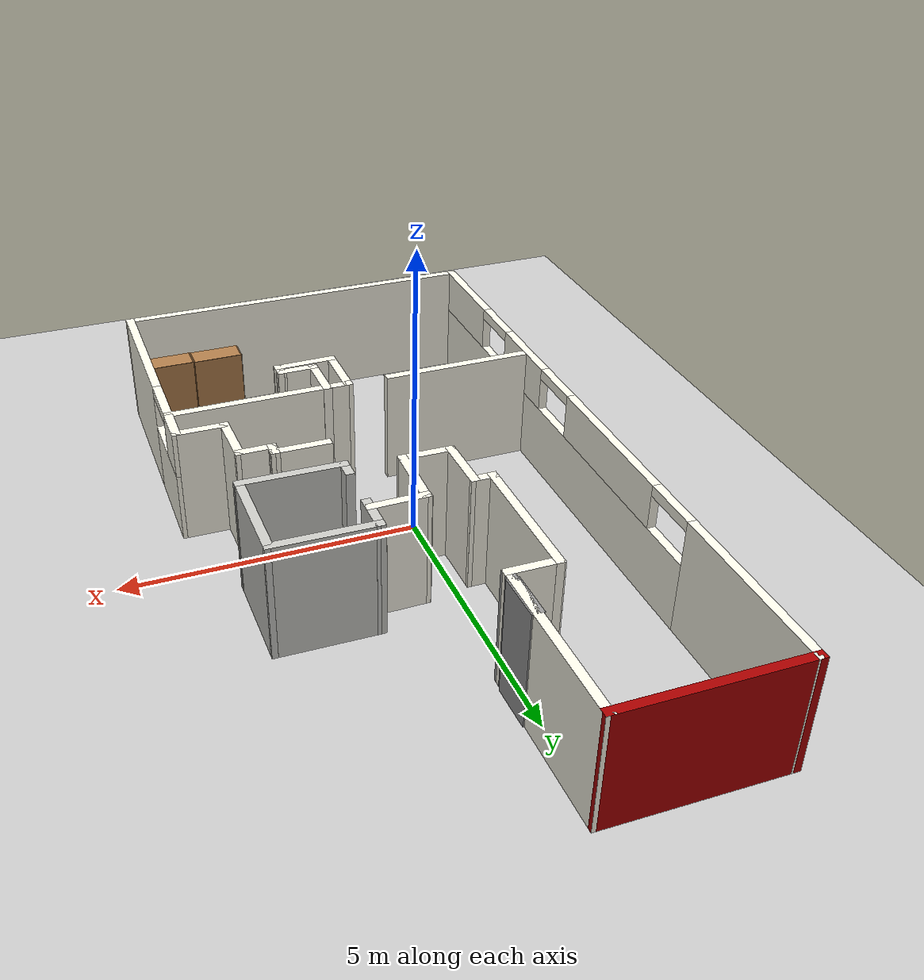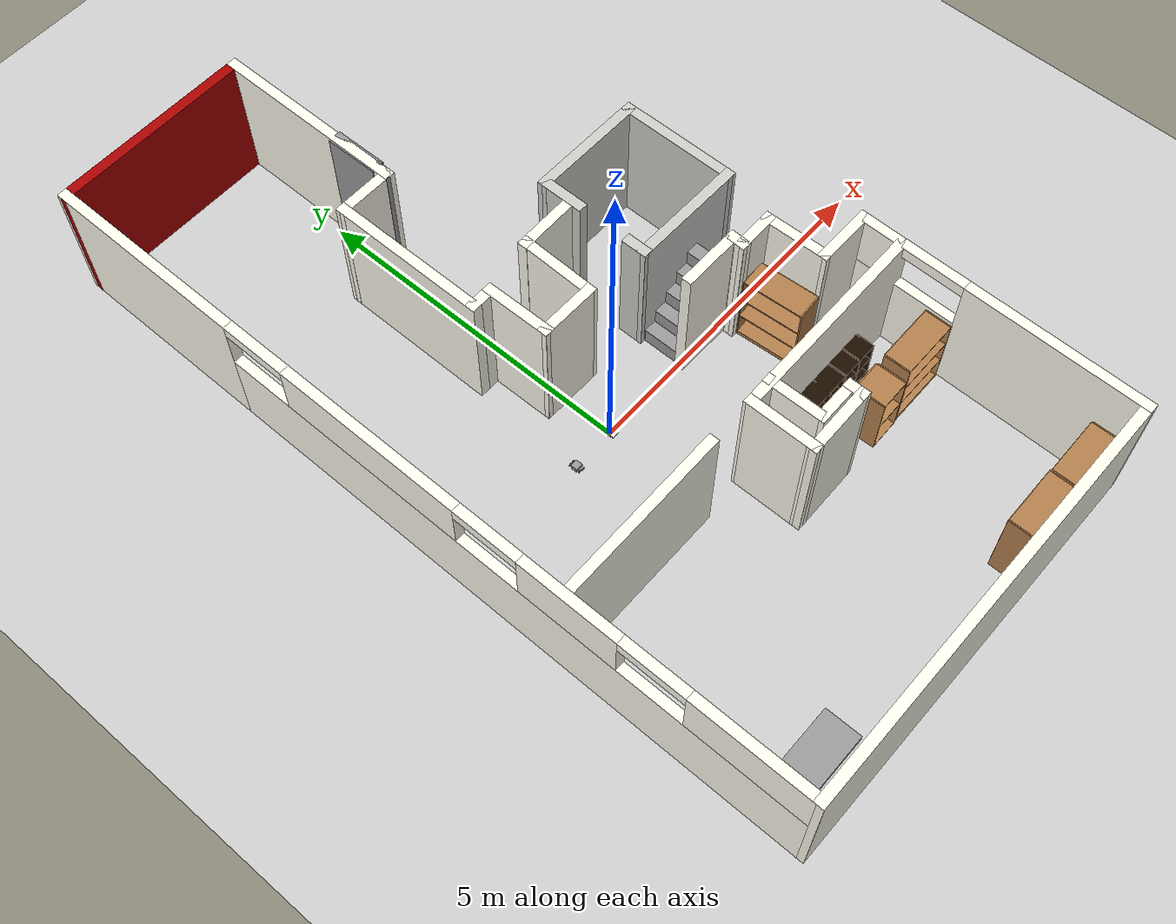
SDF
<sdf version="1.6">
 <world name="default">
  <plugin name="welcome" filename="libwelcome.so"/>
  <light name="sun" type="directional">
   <pose>0 0 10 0 -0 0</pose>
   <diffuse>0.8 0.8 0.8 1</diffuse>
   <specular>0.2 0.2 0.2 1</specular>
   <attenuation>
    <range>1000</range>
    <constant>0.9</constant>
    <linear>0.01</linear>
    <quadratic>0.001</quadratic>
   </attenuation>
   <direction>-0.5 0.1 -0.9</direction>
  </light>
  <model name="ground_plane">
   <static>1</static>
   <link name="link">
    <collision name="collision">
     <geometry><plane><normal>0 0 1</normal><size>100 100</size></plane></geometry>
     <surface>
      <contact><collide_bitmask>65535</collide_bitmask></contact>
      <friction><ode><mu>100</mu><mu2>50</mu2></ode></friction>
     </surface>
    </collision>
    <visual name="visual">
     <cast_shadows>0</cast_shadows>
     <geometry><plane><normal>0 0 1</normal><size>100 100</size></plane></geometry>
     <material>
      <script><uri>file://media/materials/scripts/gazebo.material</uri><name>Gazebo/Grey</name></script>
     </material>
    </visual>
   </link>
  </model>
  <gravity>0 0 -9.8</gravity>
  <magnetic_field>6e-06 2.3e-05 -4.2e-05</magnetic_field>
  <atmosphere type="adiabatic"/>
  <physics name="default_physics" default="0" type="ode">
   <max_step_size>0.001</max_step_size>
   <real_time_factor>1</real_time_factor>
   <real_time_update_rate>1000</real_time_update_rate>
  </physics>
  <scene><ambient>0.4 0.4 0.4 1</ambient><background>0.7 0.7 0.7 1</background><shadows>1</shadows></scene>
  <spherical_coordinates>
   <surface_model>EARTH_WGS84</surface_model>
   <latitude_deg>0</latitude_deg>
   <longitude_deg>0</longitude_deg>
   <elevation>0</elevation>
   <heading_deg>0</heading_deg>
  </spherical_coordinates>
  <model name="Apartment">
   <pose>0.435698 0.75844 0 0 -0 0</pose>
   <link name="Door_0">
    <collision name="Door_0_Collision">
     <geometry><box><size>0.792 0.2 2</size></box></geometry>
     <pose>0 0 1 0 -0 0</pose>
    </collision>
    <visual name="Door_0_Visual">
     <pose>0 0 1 0 -0 0</pose>
     <geometry><box><size>0.792 0.2 2</size></box></geometry>
     <material>
      <script><uri>file://media/materials/scripts/gazebo.material</uri><name>Gazebo/Grey</name></script>
     </material>
    </visual>
    <pose>-0.272982 3.76942 0 0 -0 1.58229</pose>
   </link>
   <link name="Stairs_1">
    <visual name="Stairs_1_Visual_0">
     <pose>1.08577 -0.451347 0.12 0 -0 1.5708</pose>
     <geometry><box><size>0.6 0.2 0.24</size></box></geometry>
     <material>
      <script><uri>file://media/materials/scripts/gazebo.material</uri><name>Gazebo/Grey</name></script>
      <ambient>1 1 1 1</ambient>
     </material>
     <meta><layer>0</layer></meta>
    </visual>
    <collision name="Stairs_1_Collision_0">
     <geometry><box><size>0.6 0.2 0.24</size></box></geometry>
     <pose>1.08577 -0.451347 0.12 0 -0 1.5708</pose>
    </collision>
    <visual name="Stairs_1_Visual_1">
     <pose>1.28577 -0.451347 0.36 0 -0 1.5708</pose>
     <geometry><box><size>0.6 0.2 0.24</size></box></geometry>
     <material>
      <script><uri>file://media/materials/scripts/gazebo.material</uri><name>Gazebo/Grey</name></script>
      <ambient>1 1 1 1</ambient>
     </material>
     <meta><layer>0</layer></meta>
    </visual>
    <collision name="Stairs_1_Collision_1">
     <geometry><box><size>0.6 0.2 0.24</size></box></geometry>
     <pose>1.28577 -0.451347 0.36 0 -0 1.5708</pose>
    </collision>
    <visual name="Stairs_1_Visual_2">
     <pose>1.48577 -0.451347 0.6 0 -0 1.5708</pose>
     <geometry><box><size>0.6 0.2 0.24</size></box></geometry>
     <material>
      <script><uri>file://media/materials/scripts/gazebo.material</uri><name>Gazebo/Grey</name></script>
      <ambient>1 1 1 1</ambient>
     </material>
     <meta><layer>0</layer></meta>
    </visual>
    <collision name="Stairs_1_Collision_2">
     <geometry><box><size>0.6 0.2 0.24</size></box></geometry>
     <pose>1.48577 -0.451347 0.6 0 -0 1.5708</pose>
    </collision>
    <visual name="Stairs_1_Visual_3">
     <pose>1.68577 -0.451347 0.84 0 -0 1.5708</pose>
     <geometry><box><size>0.6 0.2 0.24</size></box></geometry>
     <material>
      <script><uri>file://media/materials/scripts/gazebo.material</uri><name>Gazebo/Grey</name></script>
      <ambient>1 1 1 1</ambient>
     </material>
     <meta><layer>0</layer></meta>
    </visual>
    <collision name="Stairs_1_Collision_3">
     <geometry><box><size>0.6 0.2 0.24</size></box></geometry>
     <pose>1.68577 -0.451347 0.84 0 -0 1.5708</pose>
    </collision>
    <visual name="Stairs_1_Visual_4">
     <pose>1.88577 -0.451347 1.08 0 -0 1.5708</pose>
     <geometry><box><size>0.6 0.2 0.24</size></box></geometry>
     <material>
      <script><uri>file://media/materials/scripts/gazebo.material</uri><name>Gazebo/Grey</name></script>
      <ambient>1 1 1 1</ambient>
     </material>
     <meta><layer>0</layer></meta>
    </visual>
    <collision name="Stairs_1_Collision_4">
     <geometry><box><size>0.6 0.2 0.24</size></box></geometry>
     <pose>1.88577 -0.451347 1.08 0 -0 1.5708</pose>
    </collision>
   </link>
   <link name="Wall_0">
    <collision name="Wall_0_Collision">
     <geometry><box><size>2.97893 0.15 2</size></box></geometry>
     <pose>0 0 1 0 -0 0</pose>
    </collision>
    <visual name="Wall_0_Visual">
     <pose>0 0 1 0 -0 0</pose>
     <geometry><box><size>2.97893 0.15 2</size></box></geometry>
     <material>
      <script><uri>file://media/materials/scripts/gazebo.material</uri><name>Gazebo/Grey</name></script>
      <ambient>1 0.988235 0.929412 1</ambient>
     </material>
     <meta><layer>0</layer></meta>
    </visual>
    <pose>-0.276026 4.64956 0 0 -0 1.57256</pose>
   </link>
   <link name="Wall_1">
    <collision name="Wall_1_Collision">
     <geometry><box><size>3.08816 0.15 2</size></box></geometry>
     <pose>0 0 1 0 -0 0</pose>
    </collision>
    <visual name="Wall_1_Visual">
     <pose>0 0 1 0 -0 0</pose>
     <geometry><box><size>3.08816 0.15 2</size></box></geometry>
     <material>
      <script><uri>file://media/materials/scripts/gazebo.material</uri><name>Gazebo/Grey</name></script>
      <ambient>0.666667 0 0 1</ambient>
     </material>
     <meta><layer>0</layer></meta>
    </visual>
    <pose>-1.74753 6.07156 0 0 -0 3.13649</pose>
   </link>
   <link name="Wall_10">
    <collision name="Wall_10_Collision">
     <geometry><box><size>0.311078 0.15 2</size></box></geometry>
     <pose>0 0 1 0 -0 0</pose>
    </collision>
    <visual name="Wall_10_Visual">
     <pose>0 0 1 0 -0 0</pose>
     <geometry><box><size>0.311078 0.15 2</size></box></geometry>
     <material>
      <script><uri>file://media/materials/scripts/gazebo.material</uri><name>Gazebo/Grey</name></script>
      <ambient>1 0.988235 0.929412 1</ambient>
     </material>
     <meta><layer>0</layer></meta>
    </visual>
    <pose>1.87997 -0.868444 0 0 -0 1.53975</pose>
   </link>
   <link name="Wall_11">
    <collision name="Wall_11_Collision">
     <geometry><box><size>1 0.15 2</size></box></geometry>
     <pose>0 0 1 0 -0 0</pose>
    </collision>
    <visual name="Wall_11_Visual">
     <pose>0 0 1 0 -0 0</pose>
     <geometry><box><size>1 0.15 2</size></box></geometry>
     <material>
      <script><uri>file://media/materials/scripts/gazebo.material</uri><name>Gazebo/Grey</name></script>
      <ambient>1 0.988235 0.929412 1</ambient>
     </material>
     <meta><layer>0</layer></meta>
    </visual>
    <pose>1.45747 -0.784944 0 0 -0 3.13453</pose>
   </link>
   <link name="Wall_13">
    <collision name="Wall_13_Collision">
     <geometry><box><size>2.75 0.15 2</size></box></geometry>
     <pose>0 0 1 0 -0 0</pose>
    </collision>
    <visual name="Wall_13_Visual">
     <pose>0 0 1 0 -0 0</pose>
     <geometry><box><size>2.75 0.15 2</size></box></geometry>
     <material>
      <script><uri>file://media/materials/scripts/gazebo.material</uri><name>Gazebo/Grey</name></script>
      <ambient>1 0.988235 0.929412 1</ambient>
     </material>
     <meta><layer>0</layer></meta>
    </visual>
    <pose>-1.91153 -2.44094 0 0 -0 0</pose>
   </link>
   <link name="Wall_15">
    <collision name="Wall_15_Collision">
     <geometry><box><size>3.21378 0.15 2</size></box></geometry>
     <pose>0 0 1 0 -0 0</pose>
    </collision>
    <visual name="Wall_15_Visual">
     <pose>0 0 1 0 -0 0</pose>
     <geometry><box><size>3.21378 0.15 2</size></box></geometry>
     <material>
      <script><uri>file://media/materials/scripts/gazebo.material</uri><name>Gazebo/Grey</name></script>
      <ambient>1 0.988235 0.929412 1</ambient>
     </material>
     <meta><layer>0</layer></meta>
    </visual>
    <pose>1.67147 -2.45744 0 0 0 -3.138</pose>
   </link>
   <link name="Wall_16">
    <collision name="Wall_16_Collision">
     <geometry><box><size>1.1 0.15 2</size></box></geometry>
     <pose>0 0 1 0 -0 0</pose>
    </collision>
    <visual name="Wall_16_Visual">
     <pose>0 0 1 0 -0 0</pose>
     <geometry><box><size>1.1 0.15 2</size></box></geometry>
     <material>
      <script><uri>file://media/materials/scripts/gazebo.material</uri><name>Gazebo/Grey</name></script>
      <ambient>1 0.988235 0.929412 1</ambient>
     </material>
     <meta><layer>0</layer></meta>
    </visual>
    <pose>0.139474 -2.93794 0 0 0 -1.5708</pose>
   </link>
   <link name="Wall_17">
    <collision name="Wall_17_Collision">
     <geometry><box><size>1.1012 0.15 2</size></box></geometry>
     <pose>0 0 1 0 -0 0</pose>
    </collision>
    <visual name="Wall_17_Visual">
     <pose>0 0 1 0 -0 0</pose>
     <geometry><box><size>1.1012 0.15 2</size></box></geometry>
     <material>
      <script><uri>file://media/materials/scripts/gazebo.material</uri><name>Gazebo/Grey</name></script>
      <ambient>1 0.988235 0.929412 1</ambient>
     </material>
     <meta><layer>0</layer></meta>
    </visual>
    <pose>0.615474 -3.40644 0 0 -0 0.013655</pose>
   </link>
   <link name="Wall_18">
    <collision name="Wall_18_Collision">
     <geometry><box><size>0.32365 0.15 2</size></box></geometry>
     <pose>0 0 1 0 -0 0</pose>
    </collision>
    <visual name="Wall_18_Visual">
     <pose>0 0 1 0 -0 0</pose>
     <geometry><box><size>0.32365 0.15 2</size></box></geometry>
     <material>
      <script><uri>file://media/materials/scripts/gazebo.material</uri><name>Gazebo/Grey</name></script>
      <ambient>1 0.988235 0.929412 1</ambient>
     </material>
     <meta><layer>0</layer></meta>
    </visual>
    <pose>1.09147 -3.31294 0 0 -0 1.5708</pose>
   </link>
   <link name="Wall_19">
    <collision name="Wall_19_Collision">
     <geometry><box><size>0.719 0.15 2</size></box></geometry>
     <pose>0 0 1 0 -0 0</pose>
    </collision>
    <visual name="Wall_19_Visual">
     <pose>0 0 1 0 -0 0</pose>
     <geometry><box><size>0.719 0.15 2</size></box></geometry>
     <material>
      <script><uri>file://media/materials/scripts/gazebo.material</uri><name>Gazebo/Grey</name></script>
      <ambient>1 0.988235 0.929412 1</ambient>
     </material>
     <meta><layer>0</layer></meta>
    </visual>
    <pose>0.806974 -3.22744 0 0 0 -3.13632</pose>
   </link>
   <link name="Wall_2">
    <pose>-3.21653 0.012056 0 0 0 -1.5708</pose>
    <visual name="Wall_2_Visual_0">
     <pose>-4.59104 0 1 0 -0 0</pose>
     <geometry><box><size>3.10147 0.15 2</size></box></geometry>
     <material>
      <script><uri>file://media/materials/scripts/gazebo.material</uri><name>Gazebo/Grey</name></script>
      <ambient>1 0.988235 0.929412 1</ambient>
     </material>
     <meta><layer>0</layer></meta>
    </visual>
    <collision name="Wall_2_Collision_0">
     <geometry><box><size>3.10147 0.15 2</size></box></geometry>
     <pose>-4.59104 0 1 0 -0 0</pose>
    </collision>
    <visual name="Wall_2_Visual_1">
     <pose>1.55073 0 0.6095 0 -0 0</pose>
     <geometry><box><size>9.18207 0.15 1.219</size></box></geometry>
     <material>
      <script><uri>file://media/materials/scripts/gazebo.material</uri><name>Gazebo/Grey</name></script>
      <ambient>1 0.988235 0.929412 1</ambient>
     </material>
     <meta><layer>0</layer></meta>
    </visual>
    <collision name="Wall_2_Collision_1">
     <geometry><box><size>9.18207 0.15 1.219</size></box></geometry>
     <pose>1.55073 0 0.6095 0 -0 0</pose>
    </collision>
    <visual name="Wall_2_Visual_2">
     <pose>-0.630934 0 1.6095 0 -0 0</pose>
     <geometry><box><size>2.83873 0.15 0.781</size></box></geometry>
     <material>
      <script><uri>file://media/materials/scripts/gazebo.material</uri><name>Gazebo/Grey</name></script>
      <ambient>1 0.988235 0.929412 1</ambient>
     </material>
     <meta><layer>0</layer></meta>
    </visual>
    <collision name="Wall_2_Collision_2">
     <geometry><box><size>2.83873 0.15 0.781</size></box></geometry>
     <pose>-0.630934 0 1.6095 0 -0 0</pose>
    </collision>
    <visual name="Wall_2_Visual_3">
     <pose>2.53117 0 1.6095 0 -0 0</pose>
     <geometry><box><size>1.50548 0.15 0.781</size></box></geometry>
     <material>
      <script><uri>file://media/materials/scripts/gazebo.material</uri><name>Gazebo/Grey</name></script>
      <ambient>1 0.988235 0.929412 1</ambient>
     </material>
     <meta><layer>0</layer></meta>
    </visual>
    <collision name="Wall_2_Collision_3">
     <geometry><box><size>1.50548 0.15 0.781</size></box></geometry>
     <pose>2.53117 0 1.6095 0 -0 0</pose>
    </collision>
    <visual name="Wall_2_Visual_4">
     <pose>5.20784 0 1.6095 0 -0 0</pose>
     <geometry><box><size>1.86786 0.15 0.781</size></box></geometry>
     <material>
      <script><uri>file://media/materials/scripts/gazebo.material</uri><name>Gazebo/Grey</name></script>
      <ambient>1 0.988235 0.929412 1</ambient>
     </material>
     <meta><layer>0</layer></meta>
    </visual>
    <collision name="Wall_2_Collision_4">
     <geometry><box><size>1.86786 0.15 0.781</size></box></geometry>
     <pose>5.20784 0 1.6095 0 -0 0</pose>
    </collision>
    <visual name="Wall_2_Visual_5">
     <pose>-2.5453 0 1.9095 0 -0 0</pose>
     <geometry><box><size>0.99 0.15 0.181</size></box></geometry>
     <material>
      <script><uri>file://media/materials/scripts/gazebo.material</uri><name>Gazebo/Grey</name></script>
      <ambient>1 0.988235 0.929412 1</ambient>
     </material>
     <meta><layer>0</layer></meta>
    </visual>
    <collision name="Wall_2_Collision_5">
     <geometry><box><size>0.99 0.15 0.181</size></box></geometry>
     <pose>-2.5453 0 1.9095 0 -0 0</pose>
    </collision>
    <visual name="Wall_2_Visual_6">
     <pose>1.28343 0 1.9095 0 -0 0</pose>
     <geometry><box><size>0.99 0.15 0.181</size></box></geometry>
     <material>
      <script><uri>file://media/materials/scripts/gazebo.material</uri><name>Gazebo/Grey</name></script>
      <ambient>1 0.988235 0.929412 1</ambient>
     </material>
     <meta><layer>0</layer></meta>
    </visual>
    <collision name="Wall_2_Collision_6">
     <geometry><box><size>0.99 0.15 0.181</size></box></geometry>
     <pose>1.28343 0 1.9095 0 -0 0</pose>
    </collision>
    <visual name="Wall_2_Visual_7">
     <pose>3.77891 0 1.9095 0 -0 0</pose>
     <geometry><box><size>0.99 0.15 0.181</size></box></geometry>
     <material>
      <script><uri>file://media/materials/scripts/gazebo.material</uri><name>Gazebo/Grey</name></script>
      <ambient>1 0.988235 0.929412 1</ambient>
     </material>
     <meta><layer>0</layer></meta>
    </visual>
    <collision name="Wall_2_Collision_7">
     <geometry><box><size>0.99 0.15 0.181</size></box></geometry>
     <pose>3.77891 0 1.9095 0 -0 0</pose>
    </collision>
   </link>
   <link name="Wall_20">
    <collision name="Wall_20_Collision">
     <geometry><box><size>0.925382 0.15 2</size></box></geometry>
     <pose>0 0 1 0 -0 0</pose>
    </collision>
    <visual name="Wall_20_Visual">
     <pose>0 0 1 0 -0 0</pose>
     <geometry><box><size>0.925382 0.15 2</size></box></geometry>
     <material>
      <script><uri>file://media/materials/scripts/gazebo.material</uri><name>Gazebo/Grey</name></script>
      <ambient>1 0.988235 0.929412 1</ambient>
     </material>
     <meta><layer>0</layer></meta>
    </visual>
    <pose>0.519474 -2.84094 0 0 -0 1.57853</pose>
   </link>
   <link name="Wall_23">
    <collision name="Wall_23_Collision">
     <geometry><box><size>1.79124 0.15 2</size></box></geometry>
     <pose>0 0 1 0 -0 0</pose>
    </collision>
    <visual name="Wall_23_Visual">
     <pose>0 0 1 0 -0 0</pose>
     <geometry><box><size>1.79124 0.15 2</size></box></geometry>
     <material>
      <script><uri>file://media/materials/scripts/gazebo.material</uri><name>Gazebo/CeilingTiled</name></script>
      <ambient>1 1 1 1</ambient>
     </material>
     <meta><layer>0</layer></meta>
    </visual>
    <pose>1.79897 -0.097944 0 0 0 -0.015843</pose>
   </link>
   <link name="Wall_24">
    <collision name="Wall_24_Collision">
     <geometry><box><size>1.8195 0.15 2</size></box></geometry>
     <pose>0 0 1 0 -0 0</pose>
    </collision>
    <visual name="Wall_24_Visual">
     <pose>0 0 1 0 -0 0</pose>
     <geometry><box><size>1.8195 0.15 2</size></box></geometry>
     <material>
      <script><uri>file://media/materials/scripts/gazebo.material</uri><name>Gazebo/CeilingTiled</name></script>
      <ambient>1 1 1 1</ambient>
     </material>
     <meta><layer>0</layer></meta>
    </visual>
    <pose>2.61947 0.723556 0 0 -0 1.5708</pose>
   </link>
   <link name="Wall_25">
    <collision name="Wall_25_Collision">
     <geometry><box><size>1.79103 0.15 2</size></box></geometry>
     <pose>0 0 1 0 -0 0</pose>
    </collision>
    <visual name="Wall_25_Visual">
     <pose>0 0 1 0 -0 0</pose>
     <geometry><box><size>1.79103 0.15 2</size></box></geometry>
     <material>
      <script><uri>file://media/materials/scripts/gazebo.material</uri><name>Gazebo/CeilingTiled</name></script>
      <ambient>1 1 1 1</ambient>
     </material>
     <meta><layer>0</layer></meta>
    </visual>
    <pose>1.79897 1.56706 0 0 -0 3.13062</pose>
   </link>
   <link name="Wall_28">
    <collision name="Wall_28_Collision">
     <geometry><box><size>1.02916 0.15 2</size></box></geometry>
     <pose>0 0 1 0 -0 0</pose>
    </collision>
    <visual name="Wall_28_Visual">
     <pose>0 0 1 0 -0 0</pose>
     <geometry><box><size>1.02916 0.15 2</size></box></geometry>
     <material>
      <script><uri>file://media/materials/scripts/gazebo.material</uri><name>Gazebo/Grey</name></script>
      <ambient>1 0.988235 0.929412 1</ambient>
     </material>
     <meta><layer>0</layer></meta>
    </visual>
    <pose>0.535929 1.12956 0 0 0 -3.12908</pose>
   </link>
   <link name="Wall_30">
    <collision name="Wall_30_Collision">
     <geometry><box><size>1.21772 0.15 2</size></box></geometry>
     <pose>0 0 1 0 -0 0</pose>
    </collision>
    <visual name="Wall_30_Visual">
     <pose>0 0 1 0 -0 0</pose>
     <geometry><box><size>1.21772 0.15 2</size></box></geometry>
     <material>
      <script><uri>file://media/materials/scripts/gazebo.material</uri><name>Gazebo/Grey</name></script>
      <ambient>1 0.988235 0.929412 1</ambient>
     </material>
     <meta><layer>0</layer></meta>
    </visual>
    <pose>0.089183 0.590208 0 0 0 -1.5979</pose>
   </link>
   <link name="Wall_31">
    <collision name="Wall_31_Collision">
     <geometry><box><size>0.941296 0.15 2</size></box></geometry>
     <pose>0 0 1 0 -0 0</pose>
    </collision>
    <visual name="Wall_31_Visual">
     <pose>0 0 1 0 -0 0</pose>
     <geometry><box><size>0.941296 0.15 2</size></box></geometry>
     <material>
      <script><uri>file://media/materials/scripts/gazebo.material</uri><name>Gazebo/Grey</name></script>
      <ambient>1 0.988235 0.929412 1</ambient>
     </material>
     <meta><layer>0</layer></meta>
    </visual>
    <pose>-0.320908 0.061208 0 0 -0 3.12934</pose>
   </link>
   <link name="Wall_32">
    <collision name="Wall_32_Collision">
     <geometry><box><size>1.06103 0.15 2</size></box></geometry>
     <pose>0 0 1 0 -0 0</pose>
    </collision>
    <visual name="Wall_32_Visual">
     <pose>0 0 1 0 -0 0</pose>
     <geometry><box><size>1.06103 0.15 2</size></box></geometry>
     <material>
      <script><uri>file://media/materials/scripts/gazebo.material</uri><name>Gazebo/Grey</name></script>
      <ambient>1 0.988235 0.929412 1</ambient>
     </material>
     <meta><layer>0</layer></meta>
    </visual>
    <pose>-0.721026 0.521556 0 0 -0 1.58068</pose>
   </link>
   <link name="Wall_33">
    <collision name="Wall_33_Collision">
     <geometry><box><size>0.45987 0.15 2</size></box></geometry>
     <pose>0 0 1 0 -0 0</pose>
    </collision>
    <visual name="Wall_33_Visual">
     <pose>0 0 1 0 -0 0</pose>
     <geometry><box><size>0.45987 0.15 2</size></box></geometry>
     <material>
      <script><uri>file://media/materials/scripts/gazebo.material</uri><name>Gazebo/Grey</name></script>
      <ambient>1 0.988235 0.929412 1</ambient>
     </material>
     <meta><layer>0</layer></meta>
    </visual>
    <pose>-0.880526 0.977056 0 0 -0 3.14159</pose>
   </link>
   <link name="Wall_35">
    <collision name="Wall_35_Collision">
     <geometry><box><size>2.40185 0.15 2</size></box></geometry>
     <pose>0 0 1 0 -0 0</pose>
    </collision>
    <visual name="Wall_35_Visual">
     <pose>0 0 1 0 -0 0</pose>
     <geometry><box><size>2.40185 0.15 2</size></box></geometry>
     <material>
      <script><uri>file://media/materials/scripts/gazebo.material</uri><name>Gazebo/Grey</name></script>
      <ambient>1 0.988235 0.929412 1</ambient>
     </material>
     <meta><layer>0</layer></meta>
    </visual>
    <pose>-1.03553 2.10256 0 0 -0 1.5708</pose>
   </link>
   <link name="Wall_36">
    <collision name="Wall_36_Collision">
     <geometry><box><size>0.915215 0.15 2</size></box></geometry>
     <pose>0 0 1 0 -0 0</pose>
    </collision>
    <visual name="Wall_36_Visual">
     <pose>0 0 1 0 -0 0</pose>
     <geometry><box><size>0.915215 0.15 2</size></box></geometry>
     <material>
      <script><uri>file://media/materials/scripts/gazebo.material</uri><name>Gazebo/Grey</name></script>
      <ambient>1 0.988235 0.929412 1</ambient>
     </material>
     <meta><layer>0</layer></meta>
    </visual>
    <pose>-0.653026 3.22506 0 0 0 -0.007843</pose>
   </link>
   <link name="Wall_37">
    <collision name="Wall_37_Collision">
     <geometry><box><size>0.301905 0.15 2</size></box></geometry>
     <pose>0 0 1 0 -0 0</pose>
    </collision>
    <visual name="Wall_37_Visual">
     <pose>0 0 1 0 -0 0</pose>
     <geometry><box><size>0.301905 0.15 2</size></box></geometry>
     <material>
      <script><uri>file://media/materials/scripts/gazebo.material</uri><name>Gazebo/Grey</name></script>
      <ambient>1 1 1 1</ambient>
     </material>
     <meta><layer>0</layer></meta>
    </visual>
    <pose>-0.270526 3.29806 0 0 -0 1.5708</pose>
   </link>
   <link name="Wall_4">
    <collision name="Wall_4_Collision">
     <geometry><box><size>6.55531 0.15 2</size></box></geometry>
     <pose>0 0 1 0 -0 0</pose>
    </collision>
    <visual name="Wall_4_Visual">
     <pose>0 0 1 0 -0 0</pose>
     <geometry><box><size>6.55531 0.15 2</size></box></geometry>
     <material>
      <script><uri>file://media/materials/scripts/gazebo.material</uri><name>Gazebo/Grey</name></script>
      <ambient>1 0.988235 0.929412 1</ambient>
     </material>
     <meta><layer>0</layer></meta>
    </visual>
    <pose>-0.014026 -6.06694 0 0 0 -0.003747</pose>
   </link>
   <link name="Wall_42">
    <pose>0.978474 0.745556 0 0 0 -1.5708</pose>
    <visual name="Wall_42_Visual_0">
     <pose>-0.544709 0 1 0 -0 0</pose>
     <geometry><box><size>0.721287 0.15 2</size></box></geometry>
     <material>
      <script><uri>file://media/materials/scripts/gazebo.material</uri><name>Gazebo/CeilingTiled</name></script>
      <ambient>1 1 1 1</ambient>
     </material>
     <meta><layer>0</layer></meta>
    </visual>
    <collision name="Wall_42_Collision_0">
     <geometry><box><size>0.721287 0.15 2</size></box></geometry>
     <pose>-0.544709 0 1 0 -0 0</pose>
    </collision>
    <visual name="Wall_42_Visual_1">
     <pose>0.710643 0 1 0 -0 0</pose>
     <geometry><box><size>0.389419 0.15 2</size></box></geometry>
     <material>
      <script><uri>file://media/materials/scripts/gazebo.material</uri><name>Gazebo/CeilingTiled</name></script>
      <ambient>1 1 1 1</ambient>
     </material>
     <meta><layer>0</layer></meta>
    </visual>
    <collision name="Wall_42_Collision_1">
     <geometry><box><size>0.389419 0.15 2</size></box></geometry>
     <pose>0.710643 0 1 0 -0 0</pose>
    </collision>
   </link>
   <link name="Wall_5">
    <pose>3.20247 -3.96044 0 0 -0 1.56419</pose>
    <visual name="Wall_5_Visual_0">
     <pose>-0.841786 0 1 0 -0 0</pose>
     <geometry><box><size>2.70352 0.15 2</size></box></geometry>
     <material>
      <script><uri>file://media/materials/scripts/gazebo.material</uri><name>Gazebo/Grey</name></script>
      <ambient>1 0.988235 0.929412 1</ambient>
     </material>
     <meta><layer>0</layer></meta>
    </visual>
    <collision name="Wall_5_Collision_0">
     <geometry><box><size>2.70352 0.15 2</size></box></geometry>
     <pose>-0.841786 0 1 0 -0 0</pose>
    </collision>
    <visual name="Wall_5_Visual_1">
     <pose>1.35176 0 0.6095 0 -0 0</pose>
     <geometry><box><size>1.68357 0.15 1.219</size></box></geometry>
     <material>
      <script><uri>file://media/materials/scripts/gazebo.material</uri><name>Gazebo/Grey</name></script>
      <ambient>1 0.988235 0.929412 1</ambient>
     </material>
     <meta><layer>0</layer></meta>
    </visual>
    <collision name="Wall_5_Collision_1">
     <geometry><box><size>1.68357 0.15 1.219</size></box></geometry>
     <pose>1.35176 0 0.6095 0 -0 0</pose>
    </collision>
    <visual name="Wall_5_Visual_2">
     <pose>1.84676 0 1.6095 0 -0 0</pose>
     <geometry><box><size>0.693573 0.15 0.781</size></box></geometry>
     <material>
      <script><uri>file://media/materials/scripts/gazebo.material</uri><name>Gazebo/Grey</name></script>
      <ambient>1 0.988235 0.929412 1</ambient>
     </material>
     <meta><layer>0</layer></meta>
    </visual>
    <collision name="Wall_5_Collision_2">
     <geometry><box><size>0.693573 0.15 0.781</size></box></geometry>
     <pose>1.84676 0 1.6095 0 -0 0</pose>
    </collision>
    <visual name="Wall_5_Visual_3">
     <pose>1.00497 0 1.9095 0 -0 0</pose>
     <geometry><box><size>0.99 0.15 0.181</size></box></geometry>
     <material>
      <script><uri>file://media/materials/scripts/gazebo.material</uri><name>Gazebo/Grey</name></script>
      <ambient>1 0.988235 0.929412 1</ambient>
     </material>
     <meta><layer>0</layer></meta>
    </visual>
    <collision name="Wall_5_Collision_3">
     <geometry><box><size>0.99 0.15 0.181</size></box></geometry>
     <pose>1.00497 0 1.9095 0 -0 0</pose>
    </collision>
   </link>
   <link name="Wall_7">
    <collision name="Wall_7_Collision">
     <geometry><box><size>0.940612 0.15 2</size></box></geometry>
     <pose>0 0 1 0 -0 0</pose>
    </collision>
    <visual name="Wall_7_Visual">
     <pose>0 0 1 0 -0 0</pose>
     <geometry><box><size>0.940612 0.15 2</size></box></geometry>
     <material>
      <script><uri>file://media/materials/scripts/gazebo.material</uri><name>Gazebo/Grey</name></script>
      <ambient>1 0.988235 0.929412 1</ambient>
     </material>
     <meta><layer>0</layer></meta>
    </visual>
    <pose>2.82097 -1.83894 0 0 -0 3.13401</pose>
   </link>
   <link name="Wall_8">
    <collision name="Wall_8_Collision">
     <geometry><box><size>1.04134 0.15 2</size></box></geometry>
     <pose>0 0 1 0 -0 0</pose>
    </collision>
    <visual name="Wall_8_Visual">
     <pose>0 0 1 0 -0 0</pose>
     <geometry><box><size>1.04134 0.15 2</size></box></geometry>
     <material>
      <script><uri>file://media/materials/scripts/gazebo.material</uri><name>Gazebo/Grey</name></script>
      <ambient>1 0.988235 0.929412 1</ambient>
     </material>
     <meta><layer>0</layer></meta>
    </visual>
    <pose>2.41547 -1.39044 0 0 -0 1.59324</pose>
   </link>
   <link name="Wall_9">
    <collision name="Wall_9_Collision">
     <geometry><box><size>0.678216 0.15 2</size></box></geometry>
     <pose>0 0 1 0 -0 0</pose>
    </collision>
    <visual name="Wall_9_Visual">
     <pose>0 0 1 0 -0 0</pose>
     <geometry><box><size>0.678216 0.15 2</size></box></geometry>
     <material>
      <script><uri>file://media/materials/scripts/gazebo.material</uri><name>Gazebo/Grey</name></script>
      <ambient>1 0.988235 0.929412 1</ambient>
     </material>
     <meta><layer>0</layer></meta>
    </visual>
    <pose>2.14147 -0.946944 0 0 0 -3.13402</pose>
   </link>
   <static>1</static>
  </model>
  <model name="Scout">
   <link name="link_5">
    <pose>0.000124 0.000467 0.012036 0 1.5707 0</pose>
    <inertial>
     <mass>1</mass>
     <inertia>
      <ixx>0.166667</ixx>
      <ixy>0</ixy>
      <ixz>0</ixz>
      <iyy>0.166667</iyy>
      <iyz>0</iyz>
      <izz>0.166667</izz>
     </inertia>
    </inertial>
    <visual name="visual">
     <geometry><box><size>0.07 0.1 0.11</size></box></geometry>
     <material>
      <lighting>1</lighting>
      <script><uri>file://media/materials/scripts/gazebo.material</uri><name>Gazebo/Grey</name></script>
      <shader type="pixel"><normal_map>__default__</normal_map></shader>
      <ambient>0.3 0.3 0.3 1</ambient>
      <diffuse>0.7 0.7 0.7 1</diffuse>
      <specular>0.01 0.01 0.01 1</specular>
      <emissive>0 0 0 1</emissive>
     </material>
    </visual>
    <collision name="collision">
     <geometry><box><size>0.07 0.1 0.11</size></box></geometry>
     <surface>
      <friction>
       <ode><mu>1</mu><mu2>1</mu2><fdir1>0 0 0</fdir1><slip1>0</slip1><slip2>0</slip2></ode>
       <torsional>
        <coefficient>1</coefficient>
        <patch_radius>0</patch_radius>
        <surface_radius>0</surface_radius>
        <use_patch_radius>1</use_patch_radius>
        <ode><slip>0</slip></ode>
       </torsional>
      </friction>
      <bounce><restitution_coefficient>0</restitution_coefficient><threshold>1e+06</threshold></bounce>
      <contact>
       <collide_without_contact>0</collide_without_contact>
       <collide_without_contact_bitmask>1</collide_without_contact_bitmask>
       <collide_bitmask>1</collide_bitmask>
       <ode>
        <soft_cfm>0</soft_cfm>
        <soft_erp>0.2</soft_erp>
        <kp>1e+13</kp>
        <kd>1</kd>
        <max_vel>0.01</max_vel>
        <min_depth>0</min_depth>
       </ode>
       <bullet>
        <split_impulse>1</split_impulse>
        <split_impulse_penetration_threshold>-0.01</split_impulse_penetration_threshold>
        <soft_cfm>0</soft_cfm>
        <soft_erp>0.2</soft_erp>
        <kp>1e+13</kp>
        <kd>1</kd>
       </bullet>
      </contact>
     </surface>
    </collision>
   </link>
   <link name="link_6">
    <pose>0.030124 -0.082817 -0.002561 1.5707 -0 0</pose>
    <inertial>
     <mass>1</mass>
     <inertia><ixx>0.145833</ixx><ixy>0</ixy><ixz>0</ixz><iyy>0.145833</iyy><iyz>0</iyz><izz>0.125</izz></inertia>
    </inertial>
    <visual name="visual">
     <geometry><cylinder><radius>0.0254</radius><length>0.01</length></cylinder></geometry>
     <material>
      <lighting>1</lighting>
      <script><uri>file://media/materials/scripts/gazebo.material</uri><name>Gazebo/Grey</name></script>
      <shader type="pixel"><normal_map>__default__</normal_map></shader>
      <ambient>0.3 0.3 0.3 1</ambient>
      <diffuse>0.7 0.7 0.7 1</diffuse>
      <specular>0.01 0.01 0.01 1</specular>
      <emissive>0 0 0 1</emissive>
     </material>
    </visual>
    <collision name="collision">
     <geometry><cylinder><radius>0.0254</radius><length>0.01</length></cylinder></geometry>
     <surface>
      <friction>
       <ode><mu>1</mu><mu2>1</mu2><fdir1>0 0 0</fdir1><slip1>0</slip1><slip2>0</slip2></ode>
       <torsional>
        <coefficient>1</coefficient>
        <patch_radius>0</patch_radius>
        <surface_radius>0</surface_radius>
        <use_patch_radius>1</use_patch_radius>
        <ode><slip>0</slip></ode>
       </torsional>
      </friction>
      <bounce><restitution_coefficient>0</restitution_coefficient><threshold>1e+06</threshold></bounce>
      <contact>
       <collide_without_contact>0</collide_without_contact>
       <collide_without_contact_bitmask>1</collide_without_contact_bitmask>
       <collide_bitmask>1</collide_bitmask>
       <ode>
        <soft_cfm>0</soft_cfm>
        <soft_erp>0.2</soft_erp>
        <kp>1e+13</kp>
        <kd>1</kd>
        <max_vel>0.01</max_vel>
        <min_depth>0</min_depth>
       </ode>
       <bullet>
        <split_impulse>1</split_impulse>
        <split_impulse_penetration_threshold>-0.01</split_impulse_penetration_threshold>
        <soft_cfm>0</soft_cfm>
        <soft_erp>0.2</soft_erp>
        <kp>1e+13</kp>
        <kd>1</kd>
       </bullet>
      </contact>
     </surface>
    </collision>
   </link>
   <link name="link_6_clone">
    <pose>-0.029876 -0.079536 -0.002561 1.5707 -0 0</pose>
    <inertial>
     <mass>1</mass>
     <inertia><ixx>0.145833</ixx><ixy>0</ixy><ixz>0</ixz><iyy>0.145833</iyy><iyz>0</iyz><izz>0.125</izz></inertia>
    </inertial>
    <visual name="visual">
     <geometry><cylinder><radius>0.0254</radius><length>0.01</length></cylinder></geometry>
     <material>
      <lighting>1</lighting>
      <script><uri>file://media/materials/scripts/gazebo.material</uri><name>Gazebo/Grey</name></script>
      <shader type="pixel"><normal_map>__default__</normal_map></shader>
      <ambient>0.3 0.3 0.3 1</ambient>
      <diffuse>0.7 0.7 0.7 1</diffuse>
      <specular>0.01 0.01 0.01 1</specular>
      <emissive>0 0 0 1</emissive>
     </material>
    </visual>
    <collision name="collision">
     <geometry><cylinder><radius>0.0254</radius><length>0.01</length></cylinder></geometry>
     <surface>
      <friction>
       <ode><mu>1</mu><mu2>1</mu2><fdir1>0 0 0</fdir1><slip1>0</slip1><slip2>0</slip2></ode>
       <torsional>
        <coefficient>1</coefficient>
        <patch_radius>0</patch_radius>
        <surface_radius>0</surface_radius>
        <use_patch_radius>1</use_patch_radius>
        <ode><slip>0</slip></ode>
       </torsional>
      </friction>
      <bounce><restitution_coefficient>0</restitution_coefficient><threshold>1e+06</threshold></bounce>
      <contact>
       <collide_without_contact>0</collide_without_contact>
       <collide_without_contact_bitmask>1</collide_without_contact_bitmask>
       <collide_bitmask>1</collide_bitmask>
       <ode>
        <soft_cfm>0</soft_cfm>
        <soft_erp>0.2</soft_erp>
        <kp>1e+13</kp>
        <kd>1</kd>
        <max_vel>0.01</max_vel>
        <min_depth>0</min_depth>
       </ode>
       <bullet>
        <split_impulse>1</split_impulse>
        <split_impulse_penetration_threshold>-0.01</split_impulse_penetration_threshold>
        <soft_cfm>0</soft_cfm>
        <soft_erp>0.2</soft_erp>
        <kp>1e+13</kp>
        <kd>1</kd>
       </bullet>
      </contact>
     </surface>
    </collision>
   </link>
   <link name="link_6_clone_0">
    <pose>0.02967 0.080483 -0.002563 1.5707 -0 0</pose>
    <inertial>
     <mass>1</mass>
     <inertia><ixx>0.145833</ixx><ixy>0</ixy><ixz>0</ixz><iyy>0.145833</iyy><iyz>0</iyz><izz>0.125</izz></inertia>
    </inertial>
    <visual name="visual">
     <geometry><cylinder><radius>0.0254</radius><length>0.01</length></cylinder></geometry>
     <material>
      <lighting>1</lighting>
      <script><uri>file://media/materials/scripts/gazebo.material</uri><name>Gazebo/Grey</name></script>
      <shader type="pixel"><normal_map>__default__</normal_map></shader>
      <ambient>0.3 0.3 0.3 1</ambient>
      <diffuse>0.7 0.7 0.7 1</diffuse>
      <specular>0.01 0.01 0.01 1</specular>
      <emissive>0 0 0 1</emissive>
     </material>
    </visual>
    <collision name="collision">
     <geometry><cylinder><radius>0.0254</radius><length>0.01</length></cylinder></geometry>
     <surface>
      <friction>
       <ode><mu>1</mu><mu2>1</mu2><fdir1>0 0 0</fdir1><slip1>0</slip1><slip2>0</slip2></ode>
       <torsional>
        <coefficient>1</coefficient>
        <patch_radius>0</patch_radius>
        <surface_radius>0</surface_radius>
        <use_patch_radius>1</use_patch_radius>
        <ode><slip>0</slip></ode>
       </torsional>
      </friction>
      <bounce><restitution_coefficient>0</restitution_coefficient><threshold>1e+06</threshold></bounce>
      <contact>
       <collide_without_contact>0</collide_without_contact>
       <collide_without_contact_bitmask>1</collide_without_contact_bitmask>
       <collide_bitmask>1</collide_bitmask>
       <ode>
        <soft_cfm>0</soft_cfm>
        <soft_erp>0.2</soft_erp>
        <kp>1e+13</kp>
        <kd>1</kd>
        <max_vel>0.01</max_vel>
        <min_depth>0</min_depth>
       </ode>
       <bullet>
        <split_impulse>1</split_impulse>
        <split_impulse_penetration_threshold>-0.01</split_impulse_penetration_threshold>
        <soft_cfm>0</soft_cfm>
        <soft_erp>0.2</soft_erp>
        <kp>1e+13</kp>
        <kd>1</kd>
       </bullet>
      </contact>
     </surface>
    </collision>
   </link>
   <link name="link_6_clone_1">
    <pose>-0.029876 0.080469 -0.002563 1.5707 -0 0</pose>
    <inertial>
     <mass>1</mass>
     <inertia><ixx>0.145833</ixx><ixy>0</ixy><ixz>0</ixz><iyy>0.145833</iyy><iyz>0</iyz><izz>0.125</izz></inertia>
    </inertial>
    <visual name="visual">
     <geometry><cylinder><radius>0.0254</radius><length>0.01</length></cylinder></geometry>
     <material>
      <lighting>1</lighting>
      <script><uri>file://media/materials/scripts/gazebo.material</uri><name>Gazebo/Grey</name></script>
      <shader type="pixel"><normal_map>__default__</normal_map></shader>
      <ambient>0.3 0.3 0.3 1</ambient>
      <diffuse>0.7 0.7 0.7 1</diffuse>
      <specular>0.01 0.01 0.01 1</specular>
      <emissive>0 0 0 1</emissive>
     </material>
    </visual>
    <collision name="collision">
     <geometry><cylinder><radius>0.0254</radius><length>0.01</length></cylinder></geometry>
     <surface>
      <friction>
       <ode><mu>1</mu><mu2>1</mu2><fdir1>0 0 0</fdir1><slip1>0</slip1><slip2>0</slip2></ode>
       <torsional>
        <coefficient>1</coefficient>
        <patch_radius>0</patch_radius>
        <surface_radius>0</surface_radius>
        <use_patch_radius>1</use_patch_radius>
        <ode><slip>0</slip></ode>
       </torsional>
      </friction>
      <bounce><restitution_coefficient>0</restitution_coefficient><threshold>1e+06</threshold></bounce>
      <contact>
       <collide_without_contact>0</collide_without_contact>
       <collide_without_contact_bitmask>1</collide_without_contact_bitmask>
       <collide_bitmask>1</collide_bitmask>
       <ode>
        <soft_cfm>0</soft_cfm>
        <soft_erp>0.2</soft_erp>
        <kp>1e+13</kp>
        <kd>1</kd>
        <max_vel>0.01</max_vel>
        <min_depth>0</min_depth>
       </ode>
       <bullet>
        <split_impulse>1</split_impulse>
        <split_impulse_penetration_threshold>-0.01</split_impulse_penetration_threshold>
        <soft_cfm>0</soft_cfm>
        <soft_erp>0.2</soft_erp>
        <kp>1e+13</kp>
        <kd>1</kd>
       </bullet>
      </contact>
     </surface>
    </collision>
   </link>
   <link name="link_7">
    <pose>0.029712 0.000467 -0.000894 1.5707 -0 0</pose>
    <inertial>
     <mass>1</mass>
     <inertia><ixx>0.145833</ixx><ixy>0</ixy><ixz>0</ixz><iyy>0.145833</iyy><iyz>0</iyz><izz>0.125</izz></inertia>
    </inertial>
    <visual name="visual">
     <geometry><cylinder><radius>0.001</radius><length>0.15</length></cylinder></geometry>
     <material>
      <lighting>1</lighting>
      <script><uri>file://media/materials/scripts/gazebo.material</uri><name>Gazebo/Grey</name></script>
      <shader type="pixel"><normal_map>__default__</normal_map></shader>
      <ambient>0.3 0.3 0.3 1</ambient>
      <diffuse>0.7 0.7 0.7 1</diffuse>
      <specular>0.01 0.01 0.01 1</specular>
      <emissive>0 0 0 1</emissive>
     </material>
    </visual>
    <collision name="collision">
     <geometry><cylinder><radius>0.001</radius><length>0.15</length></cylinder></geometry>
     <surface>
      <friction>
       <ode><mu>1</mu><mu2>1</mu2><fdir1>0 0 0</fdir1><slip1>0</slip1><slip2>0</slip2></ode>
       <torsional>
        <coefficient>1</coefficient>
        <patch_radius>0</patch_radius>
        <surface_radius>0</surface_radius>
        <use_patch_radius>1</use_patch_radius>
        <ode><slip>0</slip></ode>
       </torsional>
      </friction>
      <bounce><restitution_coefficient>0</restitution_coefficient><threshold>1e+06</threshold></bounce>
      <contact>
       <collide_without_contact>0</collide_without_contact>
       <collide_without_contact_bitmask>1</collide_without_contact_bitmask>
       <collide_bitmask>1</collide_bitmask>
       <ode>
        <soft_cfm>0</soft_cfm>
        <soft_erp>0.2</soft_erp>
        <kp>1e+13</kp>
        <kd>1</kd>
        <max_vel>0.01</max_vel>
        <min_depth>0</min_depth>
       </ode>
       <bullet>
        <split_impulse>1</split_impulse>
        <split_impulse_penetration_threshold>-0.01</split_impulse_penetration_threshold>
        <soft_cfm>0</soft_cfm>
        <soft_erp>0.2</soft_erp>
        <kp>1e+13</kp>
        <kd>1</kd>
       </bullet>
      </contact>
     </surface>
    </collision>
   </link>
   <link name="link_7_clone">
    <pose>-0.029876 0.000467 -0.000894 1.5707 -0 0</pose>
    <inertial>
     <mass>1</mass>
     <inertia><ixx>0.145833</ixx><ixy>0</ixy><ixz>0</ixz><iyy>0.145833</iyy><iyz>0</iyz><izz>0.125</izz></inertia>
    </inertial>
    <visual name="visual">
     <geometry><cylinder><radius>0.001</radius><length>0.15</length></cylinder></geometry>
     <material>
      <lighting>1</lighting>
      <script><uri>file://media/materials/scripts/gazebo.material</uri><name>Gazebo/Grey</name></script>
      <shader type="pixel"><normal_map>__default__</normal_map></shader>
      <ambient>0.3 0.3 0.3 1</ambient>
      <diffuse>0.7 0.7 0.7 1</diffuse>
      <specular>0.01 0.01 0.01 1</specular>
      <emissive>0 0 0 1</emissive>
     </material>
    </visual>
    <collision name="collision">
     <geometry><cylinder><radius>0.001</radius><length>0.15</length></cylinder></geometry>
     <surface>
      <friction>
       <ode><mu>1</mu><mu2>1</mu2><fdir1>0 0 0</fdir1><slip1>0</slip1><slip2>0</slip2></ode>
       <torsional>
        <coefficient>1</coefficient>
        <patch_radius>0</patch_radius>
        <surface_radius>0</surface_radius>
        <use_patch_radius>1</use_patch_radius>
        <ode><slip>0</slip></ode>
       </torsional>
      </friction>
      <bounce><restitution_coefficient>0</restitution_coefficient><threshold>1e+06</threshold></bounce>
      <contact>
       <collide_without_contact>0</collide_without_contact>
       <collide_without_contact_bitmask>1</collide_without_contact_bitmask>
       <collide_bitmask>1</collide_bitmask>
       <ode>
        <soft_cfm>0</soft_cfm>
        <soft_erp>0.2</soft_erp>
        <kp>1e+13</kp>
        <kd>1</kd>
        <max_vel>0.01</max_vel>
        <min_depth>0</min_depth>
       </ode>
       <bullet>
        <split_impulse>1</split_impulse>
        <split_impulse_penetration_threshold>-0.01</split_impulse_penetration_threshold>
        <soft_cfm>0</soft_cfm>
        <soft_erp>0.2</soft_erp>
        <kp>1e+13</kp>
        <kd>1</kd>
       </bullet>
      </contact>
     </surface>
    </collision>
   </link>
   <joint name="link_5_JOINT_13" type="fixed">
    <parent>link_5</parent>
    <child>link_7</child>
    <physics>
     <ode><limit><cfm>0</cfm><erp>0.2</erp></limit><suspension><cfm>0</cfm><erp>0.2</erp></suspension></ode>
    </physics>
   </joint>
   <joint name="link_5_JOINT_14" type="fixed">
    <parent>link_5</parent>
    <child>link_7_clone</child>
    <physics>
     <ode><limit><cfm>0</cfm><erp>0.2</erp></limit><suspension><cfm>0</cfm><erp>0.2</erp></suspension></ode>
    </physics>
   </joint>
   <joint name="link_7_JOINT_12" type="revolute">
    <parent>link_7</parent>
    <child>link_6</child>
    <axis>
     <xyz>1 0 0</xyz>
     <use_parent_model_frame>0</use_parent_model_frame>
     <limit>
      <lower>-1.79769e+308</lower>
      <upper>1.79769e+308</upper>
      <effort>-1</effort>
      <velocity>-1</velocity>
     </limit>
     <dynamics>
      <spring_reference>0</spring_reference>
      <spring_stiffness>0</spring_stiffness>
      <damping>0</damping>
     </dynamics>
    </axis>
    <physics>
     <ode><limit><cfm>0</cfm><erp>0.2</erp></limit><suspension><cfm>0</cfm><erp>0.2</erp></suspension></ode>
    </physics>
   </joint>
   <joint name="link_7_JOINT_8" type="revolute">
    <parent>link_7</parent>
    <child>link_6_clone_0</child>
    <axis>
     <xyz>1 0 0</xyz>
     <use_parent_model_frame>0</use_parent_model_frame>
     <limit>
      <lower>-1.79769e+308</lower>
      <upper>1.79769e+308</upper>
      <effort>-1</effort>
      <velocity>-1</velocity>
     </limit>
     <dynamics>
      <spring_reference>0</spring_reference>
      <spring_stiffness>0</spring_stiffness>
      <damping>0</damping>
      <friction>0</friction>
     </dynamics>
    </axis>
    <physics>
     <ode><limit><cfm>0</cfm><erp>0.2</erp></limit><suspension><cfm>0</cfm><erp>0.2</erp></suspension></ode>
    </physics>
   </joint>
   <joint name="link_7_clone_JOINT_10" type="revolute">
    <parent>link_7_clone</parent>
    <child>link_6_clone_1</child>
    <axis>
     <xyz>1 0 0</xyz>
     <use_parent_model_frame>0</use_parent_model_frame>
     <limit>
      <lower>-1.79769e+308</lower>
      <upper>1.79769e+308</upper>
      <effort>-1</effort>
      <velocity>-1</velocity>
     </limit>
     <dynamics>
      <spring_reference>0</spring_reference>
      <spring_stiffness>0</spring_stiffness>
      <damping>0</damping>
      <friction>0</friction>
     </dynamics>
    </axis>
    <physics>
     <ode><limit><cfm>0</cfm><erp>0.2</erp></limit><suspension><cfm>0</cfm><erp>0.2</erp></suspension></ode>
    </physics>
   </joint>
   <joint name="link_7_clone_JOINT_11" type="revolute">
    <parent>link_7_clone</parent>
    <child>link_6_clone</child>
    <axis>
     <xyz>1 0 0</xyz>
     <use_parent_model_frame>0</use_parent_model_frame>
     <limit>
      <lower>-1.79769e+308</lower>
      <upper>1.79769e+308</upper>
      <effort>-1</effort>
      <velocity>-1</velocity>
     </limit>
     <dynamics>
      <spring_reference>0</spring_reference>
      <spring_stiffness>0</spring_stiffness>
      <damping>0</damping>
     </dynamics>
    </axis>
    <physics>
     <ode><limit><cfm>0</cfm><erp>0.2</erp></limit><suspension><cfm>0</cfm><erp>0.2</erp></suspension></ode>
    </physics>
   </joint>
   <static>0</static>
   <pose>0.018947 0.005436 0.027963 1.4e-05 2.7e-05 -0.000381</pose>
  </model>
  <model name="bookshelf">
   <static>1</static>
   <link name="link">
    <inertial><mass>1</mass></inertial>
    <collision name="back">
     <pose>0 0.005 0.6 0 -0 0</pose>
     <geometry><box><size>0.9 0.01 1.2</size></box></geometry>
    </collision>
    <visual name="visual1">
     <pose>0 0.005 0.6 0 -0 0</pose>
     <geometry><box><size>0.9 0.01 1.2</size></box></geometry>
     <material>
      <script><uri>file://media/materials/scripts/gazebo.material</uri><name>Gazebo/Wood</name></script>
     </material>
    </visual>
    <collision name="left_side">
     <pose>0.45 -0.195 0.6 0 -0 0</pose>
     <geometry><box><size>0.02 0.4 1.2</size></box></geometry>
    </collision>
    <visual name="visual2">
     <pose>0.45 -0.195 0.6 0 -0 0</pose>
     <geometry><box><size>0.02 0.4 1.2</size></box></geometry>
     <material>
      <script><uri>file://media/materials/scripts/gazebo.material</uri><name>Gazebo/Wood</name></script>
     </material>
    </visual>
    <collision name="right_side">
     <pose>-0.45 -0.195 0.6 0 -0 0</pose>
     <geometry><box><size>0.02 0.4 1.2</size></box></geometry>
    </collision>
    <visual name="visual3">
     <pose>-0.45 -0.195 0.6 0 -0 0</pose>
     <geometry><box><size>0.02 0.4 1.2</size></box></geometry>
     <material>
      <script><uri>file://media/materials/scripts/gazebo.material</uri><name>Gazebo/Wood</name></script>
     </material>
    </visual>
    <collision name="bottom">
     <pose>0 -0.195 0.03 0 -0 0</pose>
     <geometry><box><size>0.88 0.4 0.06</size></box></geometry>
    </collision>
    <visual name="visual4">
     <pose>0 -0.195 0.03 0 -0 0</pose>
     <geometry><box><size>0.88 0.4 0.06</size></box></geometry>
     <material>
      <script><uri>file://media/materials/scripts/gazebo.material</uri><name>Gazebo/Wood</name></script>
     </material>
    </visual>
    <collision name="top">
     <pose>0 -0.195 1.19 0 -0 0</pose>
     <geometry><box><size>0.88 0.4 0.02</size></box></geometry>
    </collision>
    <visual name="visual5">
     <pose>0 -0.195 1.19 0 -0 0</pose>
     <geometry><box><size>0.88 0.4 0.02</size></box></geometry>
     <material>
      <script><uri>file://media/materials/scripts/gazebo.material</uri><name>Gazebo/Wood</name></script>
     </material>
    </visual>
    <collision name="low_shelf">
     <pose>0 -0.195 0.43 0 -0 0</pose>
     <geometry><box><size>0.88 0.4 0.02</size></box></geometry>
    </collision>
    <visual name="visual6">
     <pose>0 -0.195 0.43 0 -0 0</pose>
     <geometry><box><size>0.88 0.4 0.02</size></box></geometry>
     <material>
      <script><uri>file://media/materials/scripts/gazebo.material</uri><name>Gazebo/Wood</name></script>
     </material>
    </visual>
    <collision name="high_shelf">
     <pose>0 -0.195 0.8 0 -0 0</pose>
     <geometry><box><size>0.88 0.4 0.02</size></box></geometry>
    </collision>
    <visual name="visual7">
     <pose>0 -0.195 0.8 0 -0 0</pose>
     <geometry><box><size>0.88 0.4 0.02</size></box></geometry>
     <material>
      <script><uri>file://media/materials/scripts/gazebo.material</uri><name>Gazebo/Wood</name></script>
     </material>
    </visual>
   </link>
   <pose>3.07661 -2.31495 0 0 -0 0</pose>
  </model>
  <model name="bookshelf_0">
   <static>1</static>
   <link name="link">
    <inertial><mass>1</mass></inertial>
    <collision name="back">
     <pose>0 0.005 0.6 0 -0 0</pose>
     <geometry><box><size>0.9 0.01 1.2</size></box></geometry>
    </collision>
    <visual name="visual1">
     <pose>0 0.005 0.6 0 -0 0</pose>
     <geometry><box><size>0.9 0.01 1.2</size></box></geometry>
     <material>
      <script><uri>file://media/materials/scripts/gazebo.material</uri><name>Gazebo/Wood</name></script>
     </material>
    </visual>
    <collision name="left_side">
     <pose>0.45 -0.195 0.6 0 -0 0</pose>
     <geometry><box><size>0.02 0.4 1.2</size></box></geometry>
    </collision>
    <visual name="visual2">
     <pose>0.45 -0.195 0.6 0 -0 0</pose>
     <geometry><box><size>0.02 0.4 1.2</size></box></geometry>
     <material>
      <script><uri>file://media/materials/scripts/gazebo.material</uri><name>Gazebo/Wood</name></script>
     </material>
    </visual>
    <collision name="right_side">
     <pose>-0.45 -0.195 0.6 0 -0 0</pose>
     <geometry><box><size>0.02 0.4 1.2</size></box></geometry>
    </collision>
    <visual name="visual3">
     <pose>-0.45 -0.195 0.6 0 -0 0</pose>
     <geometry><box><size>0.02 0.4 1.2</size></box></geometry>
     <material>
      <script><uri>file://media/materials/scripts/gazebo.material</uri><name>Gazebo/Wood</name></script>
     </material>
    </visual>
    <collision name="bottom">
     <pose>0 -0.195 0.03 0 -0 0</pose>
     <geometry><box><size>0.88 0.4 0.06</size></box></geometry>
    </collision>
    <visual name="visual4">
     <pose>0 -0.195 0.03 0 -0 0</pose>
     <geometry><box><size>0.88 0.4 0.06</size></box></geometry>
     <material>
      <script><uri>file://media/materials/scripts/gazebo.material</uri><name>Gazebo/Wood</name></script>
     </material>
    </visual>
    <collision name="top">
     <pose>0 -0.195 1.19 0 -0 0</pose>
     <geometry><box><size>0.88 0.4 0.02</size></box></geometry>
    </collision>
    <visual name="visual5">
     <pose>0 -0.195 1.19 0 -0 0</pose>
     <geometry><box><size>0.88 0.4 0.02</size></box></geometry>
     <material>
      <script><uri>file://media/materials/scripts/gazebo.material</uri><name>Gazebo/Wood</name></script>
     </material>
    </visual>
    <collision name="low_shelf">
     <pose>0 -0.195 0.43 0 -0 0</pose>
     <geometry><box><size>0.88 0.4 0.02</size></box></geometry>
    </collision>
    <visual name="visual6">
     <pose>0 -0.195 0.43 0 -0 0</pose>
     <geometry><box><size>0.88 0.4 0.02</size></box></geometry>
     <material>
      <script><uri>file://media/materials/scripts/gazebo.material</uri><name>Gazebo/Wood</name></script>
     </material>
    </visual>
    <collision name="high_shelf">
     <pose>0 -0.195 0.8 0 -0 0</pose>
     <geometry><box><size>0.88 0.4 0.02</size></box></geometry>
    </collision>
    <visual name="visual7">
     <pose>0 -0.195 0.8 0 -0 0</pose>
     <geometry><box><size>0.88 0.4 0.02</size></box></geometry>
     <material>
      <script><uri>file://media/materials/scripts/gazebo.material</uri><name>Gazebo/Wood</name></script>
     </material>
    </visual>
   </link>
   <pose>3.06869 -4.8324 0 0 -0 0</pose>
  </model>
  <model name="bookshelf_1">
   <static>1</static>
   <link name="link">
    <inertial><mass>1</mass></inertial>
    <collision name="back">
     <pose>0 0.005 0.6 0 -0 0</pose>
     <geometry><box><size>0.9 0.01 1.2</size></box></geometry>
    </collision>
    <visual name="visual1">
     <pose>0 0.005 0.6 0 -0 0</pose>
     <geometry><box><size>0.9 0.01 1.2</size></box></geometry>
     <material>
      <script><uri>file://media/materials/scripts/gazebo.material</uri><name>Gazebo/Wood</name></script>
     </material>
    </visual>
    <collision name="left_side">
     <pose>0.45 -0.195 0.6 0 -0 0</pose>
     <geometry><box><size>0.02 0.4 1.2</size></box></geometry>
    </collision>
    <visual name="visual2">
     <pose>0.45 -0.195 0.6 0 -0 0</pose>
     <geometry><box><size>0.02 0.4 1.2</size></box></geometry>
     <material>
      <script><uri>file://media/materials/scripts/gazebo.material</uri><name>Gazebo/Wood</name></script>
     </material>
    </visual>
    <collision name="right_side">
     <pose>-0.45 -0.195 0.6 0 -0 0</pose>
     <geometry><box><size>0.02 0.4 1.2</size></box></geometry>
    </collision>
    <visual name="visual3">
     <pose>-0.45 -0.195 0.6 0 -0 0</pose>
     <geometry><box><size>0.02 0.4 1.2</size></box></geometry>
     <material>
      <script><uri>file://media/materials/scripts/gazebo.material</uri><name>Gazebo/Wood</name></script>
     </material>
    </visual>
    <collision name="bottom">
     <pose>0 -0.195 0.03 0 -0 0</pose>
     <geometry><box><size>0.88 0.4 0.06</size></box></geometry>
    </collision>
    <visual name="visual4">
     <pose>0 -0.195 0.03 0 -0 0</pose>
     <geometry><box><size>0.88 0.4 0.06</size></box></geometry>
     <material>
      <script><uri>file://media/materials/scripts/gazebo.material</uri><name>Gazebo/Wood</name></script>
     </material>
    </visual>
    <collision name="top">
     <pose>0 -0.195 1.19 0 -0 0</pose>
     <geometry><box><size>0.88 0.4 0.02</size></box></geometry>
    </collision>
    <visual name="visual5">
     <pose>0 -0.195 1.19 0 -0 0</pose>
     <geometry><box><size>0.88 0.4 0.02</size></box></geometry>
     <material>
      <script><uri>file://media/materials/scripts/gazebo.material</uri><name>Gazebo/Wood</name></script>
     </material>
    </visual>
    <collision name="low_shelf">
     <pose>0 -0.195 0.43 0 -0 0</pose>
     <geometry><box><size>0.88 0.4 0.02</size></box></geometry>
    </collision>
    <visual name="visual6">
     <pose>0 -0.195 0.43 0 -0 0</pose>
     <geometry><box><size>0.88 0.4 0.02</size></box></geometry>
     <material>
      <script><uri>file://media/materials/scripts/gazebo.material</uri><name>Gazebo/Wood</name></script>
     </material>
    </visual>
    <collision name="high_shelf">
     <pose>0 -0.195 0.8 0 -0 0</pose>
     <geometry><box><size>0.88 0.4 0.02</size></box></geometry>
    </collision>
    <visual name="visual7">
     <pose>0 -0.195 0.8 0 -0 0</pose>
     <geometry><box><size>0.88 0.4 0.02</size></box></geometry>
     <material>
      <script><uri>file://media/materials/scripts/gazebo.material</uri><name>Gazebo/Wood</name></script>
     </material>
    </visual>
   </link>
   <pose>2.15249 -4.81844 0 0 -0 0</pose>
  </model>
  <model name="cabinet">
   <static>1</static>
   <link name="cabinet_bottom_plate">
    <inertial>
     <pose>0 0 -1 0 -0 0</pose>
     <inertia><ixx>2.05</ixx><ixy>0</ixy><ixz>0</ixz><iyy>2.05</iyy><iyz>0</iyz><izz>2.05</izz></inertia>
     <mass>25</mass>
    </inertial>
    <collision name="cabinet_bottom_plate_geom">
     <pose>0 0 0.01 0 -0 0</pose>
     <geometry><box><size>0.45 0.45 0.02</size></box></geometry>
    </collision>
    <visual name="cabinet_bottom_plate_geom_visual">
     <pose>0 0 0.01 0 -0 0</pose>
     <geometry><box><size>0.45 0.45 0.02</size></box></geometry>
     <material>
      <script><uri>file://media/materials/scripts/gazebo.material</uri><name>Gazebo/Wood</name></script>
     </material>
    </visual>
    <collision name="cabinet_bottom_plate_geom_cabinet_back_plate">
     <pose>0.235 0 0.51 0 -0 0</pose>
     <geometry><box><size>0.02 0.45 1.02</size></box></geometry>
    </collision>
    <visual name="cabinet_bottom_plate_geom_cabinet_back_plate_visual">
     <pose>0.235 0 0.51 0 -0 0</pose>
     <geometry><box><size>0.02 0.45 1.02</size></box></geometry>
     <material>
      <script><uri>file://media/materials/scripts/gazebo.material</uri><name>Gazebo/Wood</name></script>
     </material>
    </visual>
    <collision name="cabinet_bottom_plate_geom_cabinet_left_plate">
     <pose>0 0.235 0.51 0 -0 0</pose>
     <geometry><box><size>0.45 0.02 1.02</size></box></geometry>
    </collision>
    <visual name="cabinet_bottom_plate_geom_cabinet_left_plate_visual">
     <pose>0 0.235 0.51 0 -0 0</pose>
     <geometry><box><size>0.45 0.02 1.02</size></box></geometry>
     <material>
      <script><uri>file://media/materials/scripts/gazebo.material</uri><name>Gazebo/Wood</name></script>
     </material>
    </visual>
    <collision name="cabinet_bottom_plate_geom_cabinet_middle_plate">
     <pose>0 0 0.51 0 -0 0</pose>
     <geometry><box><size>0.45 0.45 0.02</size></box></geometry>
    </collision>
    <visual name="cabinet_bottom_plate_geom_cabinet_middle_plate_visual">
     <pose>0 0 0.51 0 -0 0</pose>
     <geometry><box><size>0.45 0.45 0.02</size></box></geometry>
     <material>
      <script><uri>file://media/materials/scripts/gazebo.material</uri><name>Gazebo/Wood</name></script>
     </material>
    </visual>
    <collision name="cabinet_bottom_plate_geom_cabinet_right_plate">
     <pose>0 -0.235 0.51 0 -0 0</pose>
     <geometry><box><size>0.45 0.02 1.02</size></box></geometry>
    </collision>
    <visual name="cabinet_bottom_plate_geom_cabinet_right_plate_visual">
     <pose>0 -0.235 0.51 0 -0 0</pose>
     <geometry><box><size>0.45 0.02 1.02</size></box></geometry>
     <material>
      <script><uri>file://media/materials/scripts/gazebo.material</uri><name>Gazebo/Wood</name></script>
     </material>
    </visual>
    <collision name="cabinet_bottom_plate_geom_cabinet_top_plate">
     <pose>0 0 1.01 0 -0 0</pose>
     <geometry><box><size>0.45 0.45 0.02</size></box></geometry>
    </collision>
    <visual name="cabinet_bottom_plate_geom_cabinet_top_plate_visual">
     <pose>0 0 1.01 0 -0 0</pose>
     <geometry><box><size>0.45 0.45 0.02</size></box></geometry>
     <material>
      <script><uri>file://media/materials/scripts/gazebo.material</uri><name>Gazebo/Wood</name></script>
     </material>
    </visual>
   </link>
   <pose>2.34001 -2.50112 0 0 -0 1.58728</pose>
  </model>
  <model name="6_Cube_StorageE">
   <link name="Wall_0">
    <pose>0 0 0.01 0 -0 0</pose>
    <inertial>
     <mass>1.6201</mass>
     <inertia><ixx>0.0119</ixx><iyy>0.0631</iyy><izz>0.0513</izz><ixy>0</ixy><ixz>0</ixz><iyz>0</iyz></inertia>
    </inertial>
    <collision name="Wall_0_Collision"><geometry><box><size>0.616 0.296 0.02</size></box></geometry></collision>
    <visual name="Wall_0_Visual">
     <geometry><box><size>0.616 0.296 0.02</size></box></geometry>
     <material>
      <script><uri>file://media/materials/scripts/gazebo.material</uri><name>Gazebo/Grey</name></script>
      <ambient>0.105882 0.0509804 0 1</ambient>
     </material>
    </visual>
   </link>
   <joint name="0_2" type="fixed">
    <pose>-0.308 0 0 0 -0 0</pose>
    <parent>Wall_2</parent>
    <child>Wall_0</child>
    <axis>
     <xyz>1 0 0</xyz>
     <use_parent_model_frame>0</use_parent_model_frame>
     <limit><lower>-1e+16</lower><upper>1e+16</upper></limit>
    </axis>
   </joint>
   <joint name="0_12" type="fixed">
    <parent>Wall_12</parent>
    <child>Wall_0</child>
    <axis>
     <xyz>0 0 1</xyz>
     <use_parent_model_frame>0</use_parent_model_frame>
     <limit><lower>-1e+16</lower><upper>1e+16</upper></limit>
    </axis>
   </joint>
   <joint name="0_4" type="fixed">
    <pose>0.308 0 0 0 -0 0</pose>
    <parent>Wall_4</parent>
    <child>Wall_0</child>
    <axis>
     <xyz>1 0 0</xyz>
     <use_parent_model_frame>0</use_parent_model_frame>
     <limit><lower>-1e+16</lower><upper>1e+16</upper></limit>
    </axis>
   </joint>
   <link name="Wall_10">
    <pose>0 0 0.61 0 -0 0</pose>
    <inertial>
     <mass>1.6201</mass>
     <inertia><ixx>0.0119</ixx><iyy>0.0631</iyy><izz>0.0513</izz><ixy>0</ixy><ixz>0</ixz><iyz>0</iyz></inertia>
    </inertial>
    <collision name="Wall_10_Collision"><geometry><box><size>0.616 0.296 0.02</size></box></geometry></collision>
    <visual name="Wall_10_Visual">
     <geometry><box><size>0.616 0.296 0.02</size></box></geometry>
     <material>
      <script><uri>file://media/materials/scripts/gazebo.material</uri><name>Gazebo/Grey</name></script>
      <ambient>0.105882 0.0509804 0 1</ambient>
     </material>
    </visual>
   </link>
   <joint name="10_2" type="fixed">
    <pose>-0.308 0 0 0 -0 0</pose>
    <parent>Wall_2</parent>
    <child>Wall_10</child>
    <axis>
     <xyz>1 0 0</xyz>
     <use_parent_model_frame>0</use_parent_model_frame>
     <limit><lower>-1e+16</lower><upper>1e+16</upper></limit>
    </axis>
   </joint>
   <joint name="10_12" type="fixed">
    <parent>Wall_12</parent>
    <child>Wall_10</child>
    <axis>
     <xyz>0 0 1</xyz>
     <use_parent_model_frame>0</use_parent_model_frame>
     <limit><lower>-1e+16</lower><upper>1e+16</upper></limit>
    </axis>
   </joint>
   <joint name="10_4" type="fixed">
    <pose>0.308 0 0 0 -0 0</pose>
    <parent>Wall_4</parent>
    <child>Wall_10</child>
    <axis>
     <xyz>1 0 0</xyz>
     <use_parent_model_frame>0</use_parent_model_frame>
     <limit><lower>-1e+16</lower><upper>1e+16</upper></limit>
    </axis>
   </joint>
   <link name="Wall_12">
    <pose>0 0 0.4575 0 -0 0</pose>
    <inertial>
     <mass>2.4065</mass>
     <inertia><ixx>0.0177</ixx><iyy>0.1855</iyy><izz>0.168</izz><ixy>0</ixy><ixz>0</ixz><iyz>0</iyz></inertia>
    </inertial>
    <collision name="Wall_12_Collision"><geometry><box><size>0.02 0.296 0.915</size></box></geometry></collision>
    <visual name="Wall_12_Visual">
     <geometry><box><size>0.02 0.296 0.915</size></box></geometry>
     <material>
      <script><uri>file://media/materials/scripts/gazebo.material</uri><name>Gazebo/Grey</name></script>
      <ambient>0.105882 0.0509804 0 1</ambient>
     </material>
    </visual>
   </link>
   <link name="Wall_2">
    <pose>-0.298 0 0.4575 0 -0 0</pose>
    <inertial>
     <mass>2.4065</mass>
     <inertia><ixx>0.0177</ixx><iyy>0.1855</iyy><izz>0.168</izz><ixy>0</ixy><ixz>0</ixz><iyz>0</iyz></inertia>
    </inertial>
    <collision name="Wall_2_Collision"><geometry><box><size>0.02 0.296 0.915</size></box></geometry></collision>
    <visual name="Wall_2_Visual">
     <geometry><box><size>0.02 0.296 0.915</size></box></geometry>
     <material>
      <script><uri>file://media/materials/scripts/gazebo.material</uri><name>Gazebo/Grey</name></script>
      <ambient>0.105882 0.0509804 0 1</ambient>
     </material>
    </visual>
   </link>
   <link name="Wall_4">
    <pose>0.298 0 0.4575 0 -0 0</pose>
    <inertial>
     <mass>2.4065</mass>
     <inertia><ixx>0.0177</ixx><iyy>0.1855</iyy><izz>0.168</izz><ixy>0</ixy><ixz>0</ixz><iyz>0</iyz></inertia>
    </inertial>
    <collision name="Wall_4_Collision"><geometry><box><size>0.02 0.296 0.915</size></box></geometry></collision>
    <visual name="Wall_4_Visual">
     <geometry><box><size>0.02 0.296 0.915</size></box></geometry>
     <material>
      <script><uri>file://media/materials/scripts/gazebo.material</uri><name>Gazebo/Grey</name></script>
      <ambient>0.105882 0.0509804 0 1</ambient>
     </material>
    </visual>
   </link>
   <link name="Wall_6">
    <pose>0 0 0.905 0 -0 0</pose>
    <inertial>
     <mass>1.6201</mass>
     <inertia><ixx>0.0119</ixx><iyy>0.0631</iyy><izz>0.0513</izz><ixy>0</ixy><ixz>0</ixz><iyz>0</iyz></inertia>
    </inertial>
    <collision name="Wall_6_Collision"><geometry><box><size>0.616 0.296 0.02</size></box></geometry></collision>
    <visual name="Wall_6_Visual">
     <geometry><box><size>0.616 0.296 0.02</size></box></geometry>
     <material>
      <script><uri>file://media/materials/scripts/gazebo.material</uri><name>Gazebo/Grey</name></script>
      <ambient>0.105882 0.0509804 0 1</ambient>
     </material>
    </visual>
   </link>
   <joint name="6_2" type="fixed">
    <pose>-0.308 0 0 0 -0 0</pose>
    <parent>Wall_2</parent>
    <child>Wall_6</child>
    <axis>
     <xyz>2 0 0</xyz>
     <use_parent_model_frame>0</use_parent_model_frame>
     <limit><lower>-1e+16</lower><upper>1e+16</upper></limit>
    </axis>
   </joint>
   <joint name="6_12" type="fixed">
    <parent>Wall_12</parent>
    <child>Wall_6</child>
    <axis>
     <xyz>0 0 1</xyz>
     <use_parent_model_frame>0</use_parent_model_frame>
     <limit><lower>-1e+16</lower><upper>1e+16</upper></limit>
    </axis>
   </joint>
   <joint name="6_4" type="fixed">
    <pose>0.308 0 0 0 -0 0</pose>
    <parent>Wall_4</parent>
    <child>Wall_6</child>
    <axis>
     <xyz>1 0 0</xyz>
     <use_parent_model_frame>0</use_parent_model_frame>
     <limit><lower>-1e+16</lower><upper>1e+16</upper></limit>
    </axis>
   </joint>
   <link name="Wall_8">
    <pose>0 0 0.305 0 -0 0</pose>
    <inertial>
     <mass>1.6201</mass>
     <inertia><ixx>0.0119</ixx><iyy>0.0631</iyy><izz>0.0513</izz><ixy>0</ixy><ixz>0</ixz><iyz>0</iyz></inertia>
    </inertial>
    <collision name="Wall_8_Collision"><geometry><box><size>0.616 0.296 0.02</size></box></geometry></collision>
    <visual name="Wall_8_Visual">
     <geometry><box><size>0.616 0.296 0.02</size></box></geometry>
     <material>
      <script><uri>file://media/materials/scripts/gazebo.material</uri><name>Gazebo/Grey</name></script>
      <ambient>0.105882 0.0509804 0 1</ambient>
     </material>
    </visual>
   </link>
   <joint name="8_2" type="fixed">
    <pose>-0.308 0 0 0 -0 0</pose>
    <parent>Wall_2</parent>
    <child>Wall_8</child>
    <axis>
     <xyz>1 0 0</xyz>
     <use_parent_model_frame>0</use_parent_model_frame>
     <limit><lower>-1e+16</lower><upper>1e+16</upper></limit>
    </axis>
   </joint>
   <joint name="8_12" type="fixed">
    <parent>Wall_12</parent>
    <child>Wall_8</child>
    <axis>
     <xyz>0 0 1</xyz>
     <use_parent_model_frame>0</use_parent_model_frame>
     <limit><lower>-1e+16</lower><upper>1e+16</upper></limit>
    </axis>
   </joint>
   <joint name="8_4" type="fixed">
    <pose>0.308 0 0 0 -0 0</pose>
    <parent>Wall_4</parent>
    <child>Wall_8</child>
    <axis>
     <xyz>1 0 0</xyz>
     <use_parent_model_frame>0</use_parent_model_frame>
     <limit><lower>-1e+16</lower><upper>1e+16</upper></limit>
    </axis>
   </joint>
   <static>1</static>
   <pose>1.90019 -1.90779 0 0 -0 0</pose>
  </model>
  <model name="6_Cube_StorageE_0">
   <link name="Wall_0">
    <pose>0 0 0.01 0 -0 0</pose>
    <inertial>
     <mass>1.6201</mass>
     <inertia><ixx>0.0119</ixx><iyy>0.0631</iyy><izz>0.0513</izz><ixy>0</ixy><ixz>0</ixz><iyz>0</iyz></inertia>
    </inertial>
    <collision name="Wall_0_Collision"><geometry><box><size>0.616 0.296 0.02</size></box></geometry></collision>
    <visual name="Wall_0_Visual">
     <geometry><box><size>0.616 0.296 0.02</size></box></geometry>
     <material>
      <script><uri>file://media/materials/scripts/gazebo.material</uri><name>Gazebo/Grey</name></script>
      <ambient>0.105882 0.0509804 0 1</ambient>
     </material>
    </visual>
   </link>
   <joint name="0_2" type="fixed">
    <pose>-0.308 0 0 0 -0 0</pose>
    <parent>Wall_2</parent>
    <child>Wall_0</child>
    <axis>
     <xyz>1 0 0</xyz>
     <use_parent_model_frame>0</use_parent_model_frame>
     <limit><lower>-1e+16</lower><upper>1e+16</upper></limit>
    </axis>
   </joint>
   <joint name="0_12" type="fixed">
    <parent>Wall_12</parent>
    <child>Wall_0</child>
    <axis>
     <xyz>0 0 1</xyz>
     <use_parent_model_frame>0</use_parent_model_frame>
     <limit><lower>-1e+16</lower><upper>1e+16</upper></limit>
    </axis>
   </joint>
   <joint name="0_4" type="fixed">
    <pose>0.308 0 0 0 -0 0</pose>
    <parent>Wall_4</parent>
    <child>Wall_0</child>
    <axis>
     <xyz>1 0 0</xyz>
     <use_parent_model_frame>0</use_parent_model_frame>
     <limit><lower>-1e+16</lower><upper>1e+16</upper></limit>
    </axis>
   </joint>
   <link name="Wall_10">
    <pose>0 0 0.61 0 -0 0</pose>
    <inertial>
     <mass>1.6201</mass>
     <inertia><ixx>0.0119</ixx><iyy>0.0631</iyy><izz>0.0513</izz><ixy>0</ixy><ixz>0</ixz><iyz>0</iyz></inertia>
    </inertial>
    <collision name="Wall_10_Collision"><geometry><box><size>0.616 0.296 0.02</size></box></geometry></collision>
    <visual name="Wall_10_Visual">
     <geometry><box><size>0.616 0.296 0.02</size></box></geometry>
     <material>
      <script><uri>file://media/materials/scripts/gazebo.material</uri><name>Gazebo/Grey</name></script>
      <ambient>0.105882 0.0509804 0 1</ambient>
     </material>
    </visual>
   </link>
   <joint name="10_2" type="fixed">
    <pose>-0.308 0 0 0 -0 0</pose>
    <parent>Wall_2</parent>
    <child>Wall_10</child>
    <axis>
     <xyz>1 0 0</xyz>
     <use_parent_model_frame>0</use_parent_model_frame>
     <limit><lower>-1e+16</lower><upper>1e+16</upper></limit>
    </axis>
   </joint>
   <joint name="10_12" type="fixed">
    <parent>Wall_12</parent>
    <child>Wall_10</child>
    <axis>
     <xyz>0 0 1</xyz>
     <use_parent_model_frame>0</use_parent_model_frame>
     <limit><lower>-1e+16</lower><upper>1e+16</upper></limit>
    </axis>
   </joint>
   <joint name="10_4" type="fixed">
    <pose>0.308 0 0 0 -0 0</pose>
    <parent>Wall_4</parent>
    <child>Wall_10</child>
    <axis>
     <xyz>1 0 0</xyz>
     <use_parent_model_frame>0</use_parent_model_frame>
     <limit><lower>-1e+16</lower><upper>1e+16</upper></limit>
    </axis>
   </joint>
   <link name="Wall_12">
    <pose>0 0 0.4575 0 -0 0</pose>
    <inertial>
     <mass>2.4065</mass>
     <inertia><ixx>0.0177</ixx><iyy>0.1855</iyy><izz>0.168</izz><ixy>0</ixy><ixz>0</ixz><iyz>0</iyz></inertia>
    </inertial>
    <collision name="Wall_12_Collision"><geometry><box><size>0.02 0.296 0.915</size></box></geometry></collision>
    <visual name="Wall_12_Visual">
     <geometry><box><size>0.02 0.296 0.915</size></box></geometry>
     <material>
      <script><uri>file://media/materials/scripts/gazebo.material</uri><name>Gazebo/Grey</name></script>
      <ambient>0.105882 0.0509804 0 1</ambient>
     </material>
    </visual>
   </link>
   <link name="Wall_2">
    <pose>-0.298 0 0.4575 0 -0 0</pose>
    <inertial>
     <mass>2.4065</mass>
     <inertia><ixx>0.0177</ixx><iyy>0.1855</iyy><izz>0.168</izz><ixy>0</ixy><ixz>0</ixz><iyz>0</iyz></inertia>
    </inertial>
    <collision name="Wall_2_Collision"><geometry><box><size>0.02 0.296 0.915</size></box></geometry></collision>
    <visual name="Wall_2_Visual">
     <geometry><box><size>0.02 0.296 0.915</size></box></geometry>
     <material>
      <script><uri>file://media/materials/scripts/gazebo.material</uri><name>Gazebo/Grey</name></script>
      <ambient>0.105882 0.0509804 0 1</ambient>
     </material>
    </visual>
   </link>
   <link name="Wall_4">
    <pose>0.298 0 0.4575 0 -0 0</pose>
    <inertial>
     <mass>2.4065</mass>
     <inertia><ixx>0.0177</ixx><iyy>0.1855</iyy><izz>0.168</izz><ixy>0</ixy><ixz>0</ixz><iyz>0</iyz></inertia>
    </inertial>
    <collision name="Wall_4_Collision"><geometry><box><size>0.02 0.296 0.915</size></box></geometry></collision>
    <visual name="Wall_4_Visual">
     <geometry><box><size>0.02 0.296 0.915</size></box></geometry>
     <material>
      <script><uri>file://media/materials/scripts/gazebo.material</uri><name>Gazebo/Grey</name></script>
      <ambient>0.105882 0.0509804 0 1</ambient>
     </material>
    </visual>
   </link>
   <link name="Wall_6">
    <pose>0 0 0.905 0 -0 0</pose>
    <inertial>
     <mass>1.6201</mass>
     <inertia><ixx>0.0119</ixx><iyy>0.0631</iyy><izz>0.0513</izz><ixy>0</ixy><ixz>0</ixz><iyz>0</iyz></inertia>
    </inertial>
    <collision name="Wall_6_Collision"><geometry><box><size>0.616 0.296 0.02</size></box></geometry></collision>
    <visual name="Wall_6_Visual">
     <geometry><box><size>0.616 0.296 0.02</size></box></geometry>
     <material>
      <script><uri>file://media/materials/scripts/gazebo.material</uri><name>Gazebo/Grey</name></script>
      <ambient>0.105882 0.0509804 0 1</ambient>
     </material>
    </visual>
   </link>
   <joint name="6_2" type="fixed">
    <pose>-0.308 0 0 0 -0 0</pose>
    <parent>Wall_2</parent>
    <child>Wall_6</child>
    <axis>
     <xyz>2 0 0</xyz>
     <use_parent_model_frame>0</use_parent_model_frame>
     <limit><lower>-1e+16</lower><upper>1e+16</upper></limit>
    </axis>
   </joint>
   <joint name="6_12" type="fixed">
    <parent>Wall_12</parent>
    <child>Wall_6</child>
    <axis>
     <xyz>0 0 1</xyz>
     <use_parent_model_frame>0</use_parent_model_frame>
     <limit><lower>-1e+16</lower><upper>1e+16</upper></limit>
    </axis>
   </joint>
   <joint name="6_4" type="fixed">
    <pose>0.308 0 0 0 -0 0</pose>
    <parent>Wall_4</parent>
    <child>Wall_6</child>
    <axis>
     <xyz>1 0 0</xyz>
     <use_parent_model_frame>0</use_parent_model_frame>
     <limit><lower>-1e+16</lower><upper>1e+16</upper></limit>
    </axis>
   </joint>
   <link name="Wall_8">
    <pose>0 0 0.305 0 -0 0</pose>
    <inertial>
     <mass>1.6201</mass>
     <inertia><ixx>0.0119</ixx><iyy>0.0631</iyy><izz>0.0513</izz><ixy>0</ixy><ixz>0</ixz><iyz>0</iyz></inertia>
    </inertial>
    <collision name="Wall_8_Collision"><geometry><box><size>0.616 0.296 0.02</size></box></geometry></collision>
    <visual name="Wall_8_Visual">
     <geometry><box><size>0.616 0.296 0.02</size></box></geometry>
     <material>
      <script><uri>file://media/materials/scripts/gazebo.material</uri><name>Gazebo/Grey</name></script>
      <ambient>0.105882 0.0509804 0 1</ambient>
     </material>
    </visual>
   </link>
   <joint name="8_2" type="fixed">
    <pose>-0.308 0 0 0 -0 0</pose>
    <parent>Wall_2</parent>
    <child>Wall_8</child>
    <axis>
     <xyz>1 0 0</xyz>
     <use_parent_model_frame>0</use_parent_model_frame>
     <limit><lower>-1e+16</lower><upper>1e+16</upper></limit>
    </axis>
   </joint>
   <joint name="8_12" type="fixed">
    <parent>Wall_12</parent>
    <child>Wall_8</child>
    <axis>
     <xyz>0 0 1</xyz>
     <use_parent_model_frame>0</use_parent_model_frame>
     <limit><lower>-1e+16</lower><upper>1e+16</upper></limit>
    </axis>
   </joint>
   <joint name="8_4" type="fixed">
    <pose>0.308 0 0 0 -0 0</pose>
    <parent>Wall_4</parent>
    <child>Wall_8</child>
    <axis>
     <xyz>1 0 0</xyz>
     <use_parent_model_frame>0</use_parent_model_frame>
     <limit><lower>-1e+16</lower><upper>1e+16</upper></limit>
    </axis>
   </joint>
   <static>1</static>
   <pose>2.51935 -1.90641 0 0 -0 0</pose>
  </model>
  <model name="Scout_0">
   <link name="link_5">
    <pose>0.000124 0.000467 0.012036 0 1.5707 0</pose>
    <inertial>
     <mass>1</mass>
     <inertia>
      <ixx>0.166667</ixx>
      <ixy>0</ixy>
      <ixz>0</ixz>
      <iyy>0.166667</iyy>
      <iyz>0</iyz>
      <izz>0.166667</izz>
     </inertia>
    </inertial>
    <visual name="visual">
     <geometry><box><size>0.07 0.1 0.11</size></box></geometry>
     <material>
      <lighting>1</lighting>
      <script><uri>file://media/materials/scripts/gazebo.material</uri><name>Gazebo/Grey</name></script>
      <shader type="pixel"><normal_map>__default__</normal_map></shader>
      <ambient>0.3 0.3 0.3 1</ambient>
      <diffuse>0.7 0.7 0.7 1</diffuse>
      <specular>0.01 0.01 0.01 1</specular>
      <emissive>0 0 0 1</emissive>
     </material>
    </visual>
    <collision name="collision">
     <geometry><box><size>0.07 0.1 0.11</size></box></geometry>
     <surface>
      <friction>
       <ode><mu>1</mu><mu2>1</mu2><fdir1>0 0 0</fdir1><slip1>0</slip1><slip2>0</slip2></ode>
       <torsional>
        <coefficient>1</coefficient>
        <patch_radius>0</patch_radius>
        <surface_radius>0</surface_radius>
        <use_patch_radius>1</use_patch_radius>
        <ode><slip>0</slip></ode>
       </torsional>
      </friction>
      <bounce><restitution_coefficient>0</restitution_coefficient><threshold>1e+06</threshold></bounce>
      <contact>
       <collide_without_contact>0</collide_without_contact>
       <collide_without_contact_bitmask>1</collide_without_contact_bitmask>
       <collide_bitmask>1</collide_bitmask>
       <ode>
        <soft_cfm>0</soft_cfm>
        <soft_erp>0.2</soft_erp>
        <kp>1e+13</kp>
        <kd>1</kd>
        <max_vel>0.01</max_vel>
        <min_depth>0</min_depth>
       </ode>
       <bullet>
        <split_impulse>1</split_impulse>
        <split_impulse_penetration_threshold>-0.01</split_impulse_penetration_threshold>
        <soft_cfm>0</soft_cfm>
        <soft_erp>0.2</soft_erp>
        <kp>1e+13</kp>
        <kd>1</kd>
       </bullet>
      </contact>
     </surface>
    </collision>
   </link>
   <link name="link_6">
    <pose>0.030124 -0.082817 -0.002561 1.5707 -0 0</pose>
    <inertial>
     <mass>1</mass>
     <inertia><ixx>0.145833</ixx><ixy>0</ixy><ixz>0</ixz><iyy>0.145833</iyy><iyz>0</iyz><izz>0.125</izz></inertia>
    </inertial>
    <visual name="visual">
     <geometry><cylinder><radius>0.0254</radius><length>0.01</length></cylinder></geometry>
     <material>
      <lighting>1</lighting>
      <script><uri>file://media/materials/scripts/gazebo.material</uri><name>Gazebo/Grey</name></script>
      <shader type="pixel"><normal_map>__default__</normal_map></shader>
      <ambient>0.3 0.3 0.3 1</ambient>
      <diffuse>0.7 0.7 0.7 1</diffuse>
      <specular>0.01 0.01 0.01 1</specular>
      <emissive>0 0 0 1</emissive>
     </material>
    </visual>
    <collision name="collision">
     <geometry><cylinder><radius>0.0254</radius><length>0.01</length></cylinder></geometry>
     <surface>
      <friction>
       <ode><mu>1</mu><mu2>1</mu2><fdir1>0 0 0</fdir1><slip1>0</slip1><slip2>0</slip2></ode>
       <torsional>
        <coefficient>1</coefficient>
        <patch_radius>0</patch_radius>
        <surface_radius>0</surface_radius>
        <use_patch_radius>1</use_patch_radius>
        <ode><slip>0</slip></ode>
       </torsional>
      </friction>
      <bounce><restitution_coefficient>0</restitution_coefficient><threshold>1e+06</threshold></bounce>
      <contact>
       <collide_without_contact>0</collide_without_contact>
       <collide_without_contact_bitmask>1</collide_without_contact_bitmask>
       <collide_bitmask>1</collide_bitmask>
       <ode>
        <soft_cfm>0</soft_cfm>
        <soft_erp>0.2</soft_erp>
        <kp>1e+13</kp>
        <kd>1</kd>
        <max_vel>0.01</max_vel>
        <min_depth>0</min_depth>
       </ode>
       <bullet>
        <split_impulse>1</split_impulse>
        <split_impulse_penetration_threshold>-0.01</split_impulse_penetration_threshold>
        <soft_cfm>0</soft_cfm>
        <soft_erp>0.2</soft_erp>
        <kp>1e+13</kp>
        <kd>1</kd>
       </bullet>
      </contact>
     </surface>
    </collision>
   </link>
   <link name="link_6_clone">
    <pose>-0.029876 -0.079536 -0.002561 1.5707 -0 0</pose>
    <inertial>
     <mass>1</mass>
     <inertia><ixx>0.145833</ixx><ixy>0</ixy><ixz>0</ixz><iyy>0.145833</iyy><iyz>0</iyz><izz>0.125</izz></inertia>
    </inertial>
    <visual name="visual">
     <geometry><cylinder><radius>0.0254</radius><length>0.01</length></cylinder></geometry>
     <material>
      <lighting>1</lighting>
      <script><uri>file://media/materials/scripts/gazebo.material</uri><name>Gazebo/Grey</name></script>
      <shader type="pixel"><normal_map>__default__</normal_map></shader>
      <ambient>0.3 0.3 0.3 1</ambient>
      <diffuse>0.7 0.7 0.7 1</diffuse>
      <specular>0.01 0.01 0.01 1</specular>
      <emissive>0 0 0 1</emissive>
     </material>
    </visual>
    <collision name="collision">
     <geometry><cylinder><radius>0.0254</radius><length>0.01</length></cylinder></geometry>
     <surface>
      <friction>
       <ode><mu>1</mu><mu2>1</mu2><fdir1>0 0 0</fdir1><slip1>0</slip1><slip2>0</slip2></ode>
       <torsional>
        <coefficient>1</coefficient>
        <patch_radius>0</patch_radius>
        <surface_radius>0</surface_radius>
        <use_patch_radius>1</use_patch_radius>
        <ode><slip>0</slip></ode>
       </torsional>
      </friction>
      <bounce><restitution_coefficient>0</restitution_coefficient><threshold>1e+06</threshold></bounce>
      <contact>
       <collide_without_contact>0</collide_without_contact>
       <collide_without_contact_bitmask>1</collide_without_contact_bitmask>
       <collide_bitmask>1</collide_bitmask>
       <ode>
        <soft_cfm>0</soft_cfm>
        <soft_erp>0.2</soft_erp>
        <kp>1e+13</kp>
        <kd>1</kd>
        <max_vel>0.01</max_vel>
        <min_depth>0</min_depth>
       </ode>
       <bullet>
        <split_impulse>1</split_impulse>
        <split_impulse_penetration_threshold>-0.01</split_impulse_penetration_threshold>
        <soft_cfm>0</soft_cfm>
        <soft_erp>0.2</soft_erp>
        <kp>1e+13</kp>
        <kd>1</kd>
       </bullet>
      </contact>
     </surface>
    </collision>
   </link>
   <link name="link_6_clone_0">
    <pose>0.02967 0.080483 -0.002563 1.5707 -0 0</pose>
    <inertial>
     <mass>1</mass>
     <inertia><ixx>0.145833</ixx><ixy>0</ixy><ixz>0</ixz><iyy>0.145833</iyy><iyz>0</iyz><izz>0.125</izz></inertia>
    </inertial>
    <visual name="visual">
     <geometry><cylinder><radius>0.0254</radius><length>0.01</length></cylinder></geometry>
     <material>
      <lighting>1</lighting>
      <script><uri>file://media/materials/scripts/gazebo.material</uri><name>Gazebo/Grey</name></script>
      <shader type="pixel"><normal_map>__default__</normal_map></shader>
      <ambient>0.3 0.3 0.3 1</ambient>
      <diffuse>0.7 0.7 0.7 1</diffuse>
      <specular>0.01 0.01 0.01 1</specular>
      <emissive>0 0 0 1</emissive>
     </material>
    </visual>
    <collision name="collision">
     <geometry><cylinder><radius>0.0254</radius><length>0.01</length></cylinder></geometry>
     <surface>
      <friction>
       <ode><mu>1</mu><mu2>1</mu2><fdir1>0 0 0</fdir1><slip1>0</slip1><slip2>0</slip2></ode>
       <torsional>
        <coefficient>1</coefficient>
        <patch_radius>0</patch_radius>
        <surface_radius>0</surface_radius>
        <use_patch_radius>1</use_patch_radius>
        <ode><slip>0</slip></ode>
       </torsional>
      </friction>
      <bounce><restitution_coefficient>0</restitution_coefficient><threshold>1e+06</threshold></bounce>
      <contact>
       <collide_without_contact>0</collide_without_contact>
       <collide_without_contact_bitmask>1</collide_without_contact_bitmask>
       <collide_bitmask>1</collide_bitmask>
       <ode>
        <soft_cfm>0</soft_cfm>
        <soft_erp>0.2</soft_erp>
        <kp>1e+13</kp>
        <kd>1</kd>
        <max_vel>0.01</max_vel>
        <min_depth>0</min_depth>
       </ode>
       <bullet>
        <split_impulse>1</split_impulse>
        <split_impulse_penetration_threshold>-0.01</split_impulse_penetration_threshold>
        <soft_cfm>0</soft_cfm>
        <soft_erp>0.2</soft_erp>
        <kp>1e+13</kp>
        <kd>1</kd>
       </bullet>
      </contact>
     </surface>
    </collision>
   </link>
   <link name="link_6_clone_1">
    <pose>-0.029876 0.080469 -0.002563 1.5707 -0 0</pose>
    <inertial>
     <mass>1</mass>
     <inertia><ixx>0.145833</ixx><ixy>0</ixy><ixz>0</ixz><iyy>0.145833</iyy><iyz>0</iyz><izz>0.125</izz></inertia>
    </inertial>
    <visual name="visual">
     <geometry><cylinder><radius>0.0254</radius><length>0.01</length></cylinder></geometry>
     <material>
      <lighting>1</lighting>
      <script><uri>file://media/materials/scripts/gazebo.material</uri><name>Gazebo/Grey</name></script>
      <shader type="pixel"><normal_map>__default__</normal_map></shader>
      <ambient>0.3 0.3 0.3 1</ambient>
      <diffuse>0.7 0.7 0.7 1</diffuse>
      <specular>0.01 0.01 0.01 1</specular>
      <emissive>0 0 0 1</emissive>
     </material>
    </visual>
    <collision name="collision">
     <geometry><cylinder><radius>0.0254</radius><length>0.01</length></cylinder></geometry>
     <surface>
      <friction>
       <ode><mu>1</mu><mu2>1</mu2><fdir1>0 0 0</fdir1><slip1>0</slip1><slip2>0</slip2></ode>
       <torsional>
        <coefficient>1</coefficient>
        <patch_radius>0</patch_radius>
        <surface_radius>0</surface_radius>
        <use_patch_radius>1</use_patch_radius>
        <ode><slip>0</slip></ode>
       </torsional>
      </friction>
      <bounce><restitution_coefficient>0</restitution_coefficient><threshold>1e+06</threshold></bounce>
      <contact>
       <collide_without_contact>0</collide_without_contact>
       <collide_without_contact_bitmask>1</collide_without_contact_bitmask>
       <collide_bitmask>1</collide_bitmask>
       <ode>
        <soft_cfm>0</soft_cfm>
        <soft_erp>0.2</soft_erp>
        <kp>1e+13</kp>
        <kd>1</kd>
        <max_vel>0.01</max_vel>
        <min_depth>0</min_depth>
       </ode>
       <bullet>
        <split_impulse>1</split_impulse>
        <split_impulse_penetration_threshold>-0.01</split_impulse_penetration_threshold>
        <soft_cfm>0</soft_cfm>
        <soft_erp>0.2</soft_erp>
        <kp>1e+13</kp>
        <kd>1</kd>
       </bullet>
      </contact>
     </surface>
    </collision>
   </link>
   <link name="link_7">
    <pose>0.029712 0.000467 -0.000894 1.5707 -0 0</pose>
    <inertial>
     <mass>1</mass>
     <inertia><ixx>0.145833</ixx><ixy>0</ixy><ixz>0</ixz><iyy>0.145833</iyy><iyz>0</iyz><izz>0.125</izz></inertia>
    </inertial>
    <visual name="visual">
     <geometry><cylinder><radius>0.001</radius><length>0.15</length></cylinder></geometry>
     <material>
      <lighting>1</lighting>
      <script><uri>file://media/materials/scripts/gazebo.material</uri><name>Gazebo/Grey</name></script>
      <shader type="pixel"><normal_map>__default__</normal_map></shader>
      <ambient>0.3 0.3 0.3 1</ambient>
      <diffuse>0.7 0.7 0.7 1</diffuse>
      <specular>0.01 0.01 0.01 1</specular>
      <emissive>0 0 0 1</emissive>
     </material>
    </visual>
    <collision name="collision">
     <geometry><cylinder><radius>0.001</radius><length>0.15</length></cylinder></geometry>
     <surface>
      <friction>
       <ode><mu>1</mu><mu2>1</mu2><fdir1>0 0 0</fdir1><slip1>0</slip1><slip2>0</slip2></ode>
       <torsional>
        <coefficient>1</coefficient>
        <patch_radius>0</patch_radius>
        <surface_radius>0</surface_radius>
        <use_patch_radius>1</use_patch_radius>
        <ode><slip>0</slip></ode>
       </torsional>
      </friction>
      <bounce><restitution_coefficient>0</restitution_coefficient><threshold>1e+06</threshold></bounce>
      <contact>
       <collide_without_contact>0</collide_without_contact>
       <collide_without_contact_bitmask>1</collide_without_contact_bitmask>
       <collide_bitmask>1</collide_bitmask>
       <ode>
        <soft_cfm>0</soft_cfm>
        <soft_erp>0.2</soft_erp>
        <kp>1e+13</kp>
        <kd>1</kd>
        <max_vel>0.01</max_vel>
        <min_depth>0</min_depth>
       </ode>
       <bullet>
        <split_impulse>1</split_impulse>
        <split_impulse_penetration_threshold>-0.01</split_impulse_penetration_threshold>
        <soft_cfm>0</soft_cfm>
        <soft_erp>0.2</soft_erp>
        <kp>1e+13</kp>
        <kd>1</kd>
       </bullet>
      </contact>
     </surface>
    </collision>
   </link>
   <link name="link_7_clone">
    <pose>-0.029876 0.000467 -0.000894 1.5707 -0 0</pose>
    <inertial>
     <mass>1</mass>
     <inertia><ixx>0.145833</ixx><ixy>0</ixy><ixz>0</ixz><iyy>0.145833</iyy><iyz>0</iyz><izz>0.125</izz></inertia>
    </inertial>
    <visual name="visual">
     <geometry><cylinder><radius>0.001</radius><length>0.15</length></cylinder></geometry>
     <material>
      <lighting>1</lighting>
      <script><uri>file://media/materials/scripts/gazebo.material</uri><name>Gazebo/Grey</name></script>
      <shader type="pixel"><normal_map>__default__</normal_map></shader>
      <ambient>0.3 0.3 0.3 1</ambient>
      <diffuse>0.7 0.7 0.7 1</diffuse>
      <specular>0.01 0.01 0.01 1</specular>
      <emissive>0 0 0 1</emissive>
     </material>
    </visual>
    <collision name="collision">
     <geometry><cylinder><radius>0.001</radius><length>0.15</length></cylinder></geometry>
     <surface>
      <friction>
       <ode><mu>1</mu><mu2>1</mu2><fdir1>0 0 0</fdir1><slip1>0</slip1><slip2>0</slip2></ode>
       <torsional>
        <coefficient>1</coefficient>
        <patch_radius>0</patch_radius>
        <surface_radius>0</surface_radius>
        <use_patch_radius>1</use_patch_radius>
        <ode><slip>0</slip></ode>
       </torsional>
      </friction>
      <bounce><restitution_coefficient>0</restitution_coefficient><threshold>1e+06</threshold></bounce>
      <contact>
       <collide_without_contact>0</collide_without_contact>
       <collide_without_contact_bitmask>1</collide_without_contact_bitmask>
       <collide_bitmask>1</collide_bitmask>
       <ode>
        <soft_cfm>0</soft_cfm>
        <soft_erp>0.2</soft_erp>
        <kp>1e+13</kp>
        <kd>1</kd>
        <max_vel>0.01</max_vel>
        <min_depth>0</min_depth>
       </ode>
       <bullet>
        <split_impulse>1</split_impulse>
        <split_impulse_penetration_threshold>-0.01</split_impulse_penetration_threshold>
        <soft_cfm>0</soft_cfm>
        <soft_erp>0.2</soft_erp>
        <kp>1e+13</kp>
        <kd>1</kd>
       </bullet>
      </contact>
     </surface>
    </collision>
   </link>
   <joint name="link_5_JOINT_13" type="fixed">
    <parent>link_5</parent>
    <child>link_7</child>
    <physics>
     <ode><limit><cfm>0</cfm><erp>0.2</erp></limit><suspension><cfm>0</cfm><erp>0.2</erp></suspension></ode>
    </physics>
   </joint>
   <joint name="link_5_JOINT_14" type="fixed">
    <parent>link_5</parent>
    <child>link_7_clone</child>
    <physics>
     <ode><limit><cfm>0</cfm><erp>0.2</erp></limit><suspension><cfm>0</cfm><erp>0.2</erp></suspension></ode>
    </physics>
   </joint>
   <joint name="link_7_JOINT_12" type="revolute">
    <parent>link_7</parent>
    <child>link_6</child>
    <axis>
     <xyz>1 0 0</xyz>
     <use_parent_model_frame>0</use_parent_model_frame>
     <limit>
      <lower>-1.79769e+308</lower>
      <upper>1.79769e+308</upper>
      <effort>-1</effort>
      <velocity>-1</velocity>
     </limit>
     <dynamics>
      <spring_reference>0</spring_reference>
      <spring_stiffness>0</spring_stiffness>
      <damping>0</damping>
     </dynamics>
    </axis>
    <physics>
     <ode><limit><cfm>0</cfm><erp>0.2</erp></limit><suspension><cfm>0</cfm><erp>0.2</erp></suspension></ode>
    </physics>
   </joint>
   <joint name="link_7_JOINT_8" type="revolute">
    <parent>link_7</parent>
    <child>link_6_clone_0</child>
    <axis>
     <xyz>1 0 0</xyz>
     <use_parent_model_frame>0</use_parent_model_frame>
     <limit>
      <lower>-1.79769e+308</lower>
      <upper>1.79769e+308</upper>
      <effort>-1</effort>
      <velocity>-1</velocity>
     </limit>
     <dynamics>
      <spring_reference>0</spring_reference>
      <spring_stiffness>0</spring_stiffness>
      <damping>0</damping>
      <friction>0</friction>
     </dynamics>
    </axis>
    <physics>
     <ode><limit><cfm>0</cfm><erp>0.2</erp></limit><suspension><cfm>0</cfm><erp>0.2</erp></suspension></ode>
    </physics>
   </joint>
   <joint name="link_7_clone_JOINT_10" type="revolute">
    <parent>link_7_clone</parent>
    <child>link_6_clone_1</child>
    <axis>
     <xyz>1 0 0</xyz>
     <use_parent_model_frame>0</use_parent_model_frame>
     <limit>
      <lower>-1.79769e+308</lower>
      <upper>1.79769e+308</upper>
      <effort>-1</effort>
      <velocity>-1</velocity>
     </limit>
     <dynamics>
      <spring_reference>0</spring_reference>
      <spring_stiffness>0</spring_stiffness>
      <damping>0</damping>
      <friction>0</friction>
     </dynamics>
    </axis>
    <physics>
     <ode><limit><cfm>0</cfm><erp>0.2</erp></limit><suspension><cfm>0</cfm><erp>0.2</erp></suspension></ode>
    </physics>
   </joint>
   <joint name="link_7_clone_JOINT_11" type="revolute">
    <parent>link_7_clone</parent>
    <child>link_6_clone</child>
    <axis>
     <xyz>1 0 0</xyz>
     <use_parent_model_frame>0</use_parent_model_frame>
     <limit>
      <lower>-1.79769e+308</lower>
      <upper>1.79769e+308</upper>
      <effort>-1</effort>
      <velocity>-1</velocity>
     </limit>
     <dynamics>
      <spring_reference>0</spring_reference>
      <spring_stiffness>0</spring_stiffness>
      <damping>0</damping>
     </dynamics>
    </axis>
    <physics>
     <ode><limit><cfm>0</cfm><erp>0.2</erp></limit><suspension><cfm>0</cfm><erp>0.2</erp></suspension></ode>
    </physics>
   </joint>
   <static>0</static>
   <pose>-0.667909 -0.004186 0.027963 1.4e-05 2.7e-05 -0.000102</pose>
  </model>
  <model name="bookshelf_2">
   <static>1</static>
   <link name="link">
    <inertial><mass>1</mass></inertial>
    <collision name="back">
     <pose>0 0.005 0.6 0 -0 0</pose>
     <geometry><box><size>0.9 0.01 1.2</size></box></geometry>
    </collision>
    <visual name="visual1">
     <pose>0 0.005 0.6 0 -0 0</pose>
     <geometry><box><size>0.9 0.01 1.2</size></box></geometry>
     <material>
      <script><uri>file://media/materials/scripts/gazebo.material</uri><name>Gazebo/Wood</name></script>
     </material>
    </visual>
    <collision name="left_side">
     <pose>0.45 -0.195 0.6 0 -0 0</pose>
     <geometry><box><size>0.02 0.4 1.2</size></box></geometry>
    </collision>
    <visual name="visual2">
     <pose>0.45 -0.195 0.6 0 -0 0</pose>
     <geometry><box><size>0.02 0.4 1.2</size></box></geometry>
     <material>
      <script><uri>file://media/materials/scripts/gazebo.material</uri><name>Gazebo/Wood</name></script>
     </material>
    </visual>
    <collision name="right_side">
     <pose>-0.45 -0.195 0.6 0 -0 0</pose>
     <geometry><box><size>0.02 0.4 1.2</size></box></geometry>
    </collision>
    <visual name="visual3">
     <pose>-0.45 -0.195 0.6 0 -0 0</pose>
     <geometry><box><size>0.02 0.4 1.2</size></box></geometry>
     <material>
      <script><uri>file://media/materials/scripts/gazebo.material</uri><name>Gazebo/Wood</name></script>
     </material>
    </visual>
    <collision name="bottom">
     <pose>0 -0.195 0.03 0 -0 0</pose>
     <geometry><box><size>0.88 0.4 0.06</size></box></geometry>
    </collision>
    <visual name="visual4">
     <pose>0 -0.195 0.03 0 -0 0</pose>
     <geometry><box><size>0.88 0.4 0.06</size></box></geometry>
     <material>
      <script><uri>file://media/materials/scripts/gazebo.material</uri><name>Gazebo/Wood</name></script>
     </material>
    </visual>
    <collision name="top">
     <pose>0 -0.195 1.19 0 -0 0</pose>
     <geometry><box><size>0.88 0.4 0.02</size></box></geometry>
    </collision>
    <visual name="visual5">
     <pose>0 -0.195 1.19 0 -0 0</pose>
     <geometry><box><size>0.88 0.4 0.02</size></box></geometry>
     <material>
      <script><uri>file://media/materials/scripts/gazebo.material</uri><name>Gazebo/Wood</name></script>
     </material>
    </visual>
    <collision name="low_shelf">
     <pose>0 -0.195 0.43 0 -0 0</pose>
     <geometry><box><size>0.88 0.4 0.02</size></box></geometry>
    </collision>
    <visual name="visual6">
     <pose>0 -0.195 0.43 0 -0 0</pose>
     <geometry><box><size>0.88 0.4 0.02</size></box></geometry>
     <material>
      <script><uri>file://media/materials/scripts/gazebo.material</uri><name>Gazebo/Wood</name></script>
     </material>
    </visual>
    <collision name="high_shelf">
     <pose>0 -0.195 0.8 0 -0 0</pose>
     <geometry><box><size>0.88 0.4 0.02</size></box></geometry>
    </collision>
    <visual name="visual7">
     <pose>0 -0.195 0.8 0 -0 0</pose>
     <geometry><box><size>0.88 0.4 0.02</size></box></geometry>
     <material>
      <script><uri>file://media/materials/scripts/gazebo.material</uri><name>Gazebo/Wood</name></script>
     </material>
    </visual>
   </link>
   <pose>2.75185 -0.692736 0 0 0 -1.50438</pose>
  </model>
  <model name="unit_box_1_clone">
   <pose>-1.72374 -4.71484 0.058964 0 -0 3.7e-05</pose>
   <link name="link">
    <inertial>
     <mass>1</mass>
     <inertia>
      <ixx>0.166667</ixx>
      <ixy>0</ixy>
      <ixz>0</ixz>
      <iyy>0.166667</iyy>
      <iyz>0</iyz>
      <izz>0.166667</izz>
     </inertia>
    </inertial>
    <collision name="collision"><geometry><box><size>1 0.550173 0.117928</size></box></geometry></collision>
    <visual name="visual">
     <geometry><box><size>1 0.550173 0.117928</size></box></geometry>
     <material>
      <script><name>Gazebo/Grey</name><uri>file://media/materials/scripts/gazebo.material</uri></script>
     </material>
    </visual>
   </link>
  </model>
  <light name="user_spot_light_0" type="spot">
   <pose>-2.56319 1.52675 1 0 -0 0</pose>
   <diffuse>0.5 0.5 0.5 1</diffuse>
   <specular>0.1 0.1 0.1 1</specular>
   <direction>0 0 -1</direction>
   <attenuation>
    <range>20</range>
    <constant>0.5</constant>
    <linear>0.01</linear>
    <quadratic>0.001</quadratic>
   </attenuation>
   <cast_shadows>0</cast_shadows>
   <spot><inner_angle>0.6</inner_angle><outer_angle>1</outer_angle><falloff>1</falloff></spot>
  </light>
  <light name="user_spot_light_1" type="spot">
   <pose>-0.382779 1.14988 1 0 -0 0</pose>
   <diffuse>0.5 0.5 0.5 1</diffuse>
   <specular>0.1 0.1 0.1 1</specular>
   <direction>0 0 -1</direction>
   <attenuation>
    <range>20</range>
    <constant>0.5</constant>
    <linear>0.01</linear>
    <quadratic>0.001</quadratic>
   </attenuation>
   <cast_shadows>0</cast_shadows>
   <spot><inner_angle>0.6</inner_angle><outer_angle>1</outer_angle><falloff>1</falloff></spot>
  </light>
  <light name="user_point_light_0" type="point">
   <pose>-18.6472 1.6867 1 0 -0 0</pose>
   <diffuse>0.5 0.5 0.5 1</diffuse>
   <specular>0.1 0.1 0.1 1</specular>
   <attenuation>
    <range>20</range>
    <constant>0.5</constant>
    <linear>0.01</linear>
    <quadratic>0.001</quadratic>
   </attenuation>
   <cast_shadows>0</cast_shadows>
   <direction>0 0 -1</direction>
  </light>
 </world>
</sdf>
